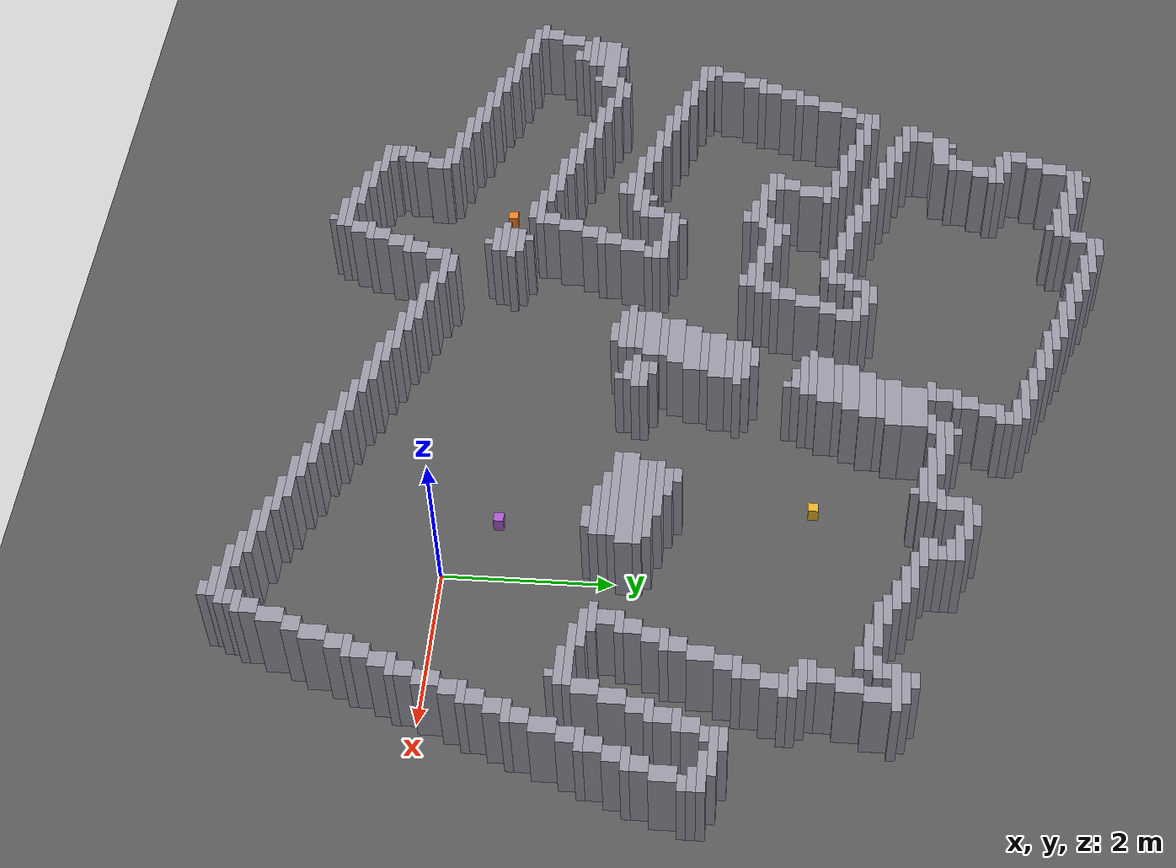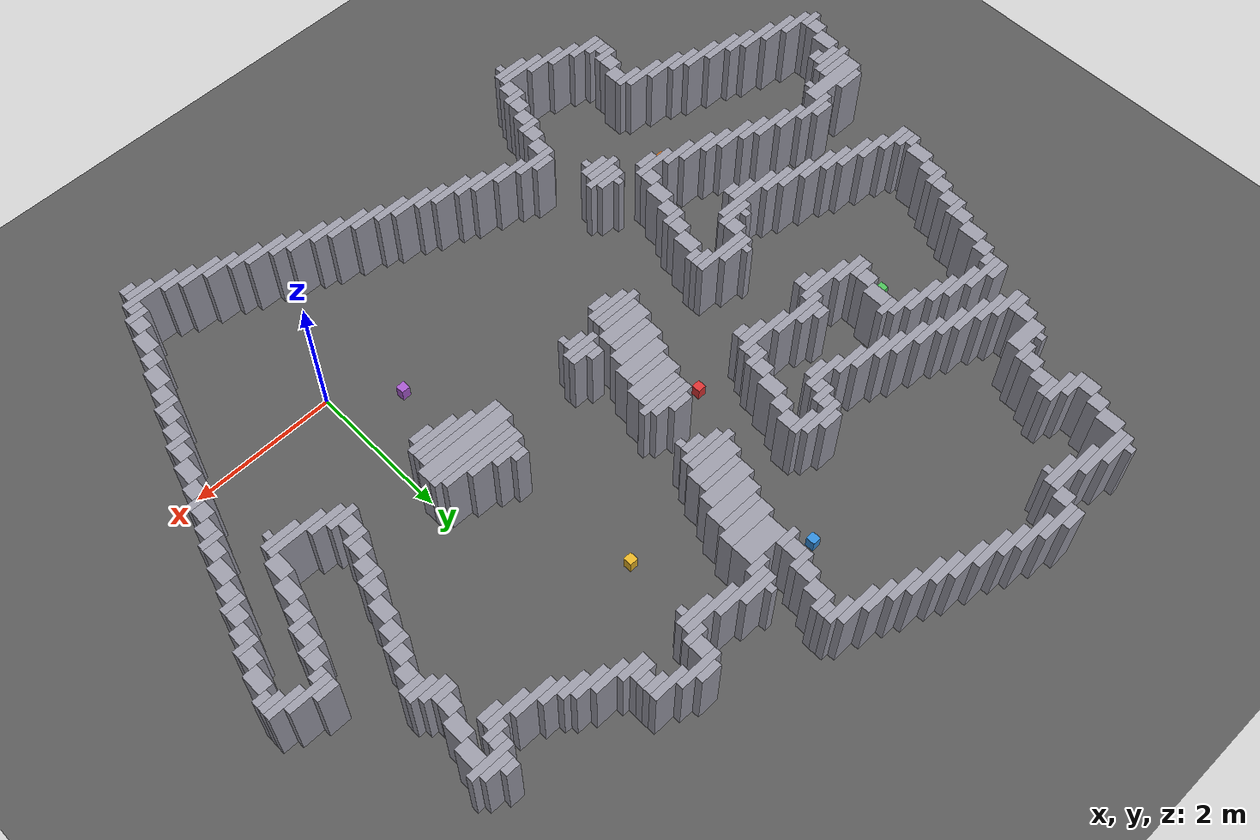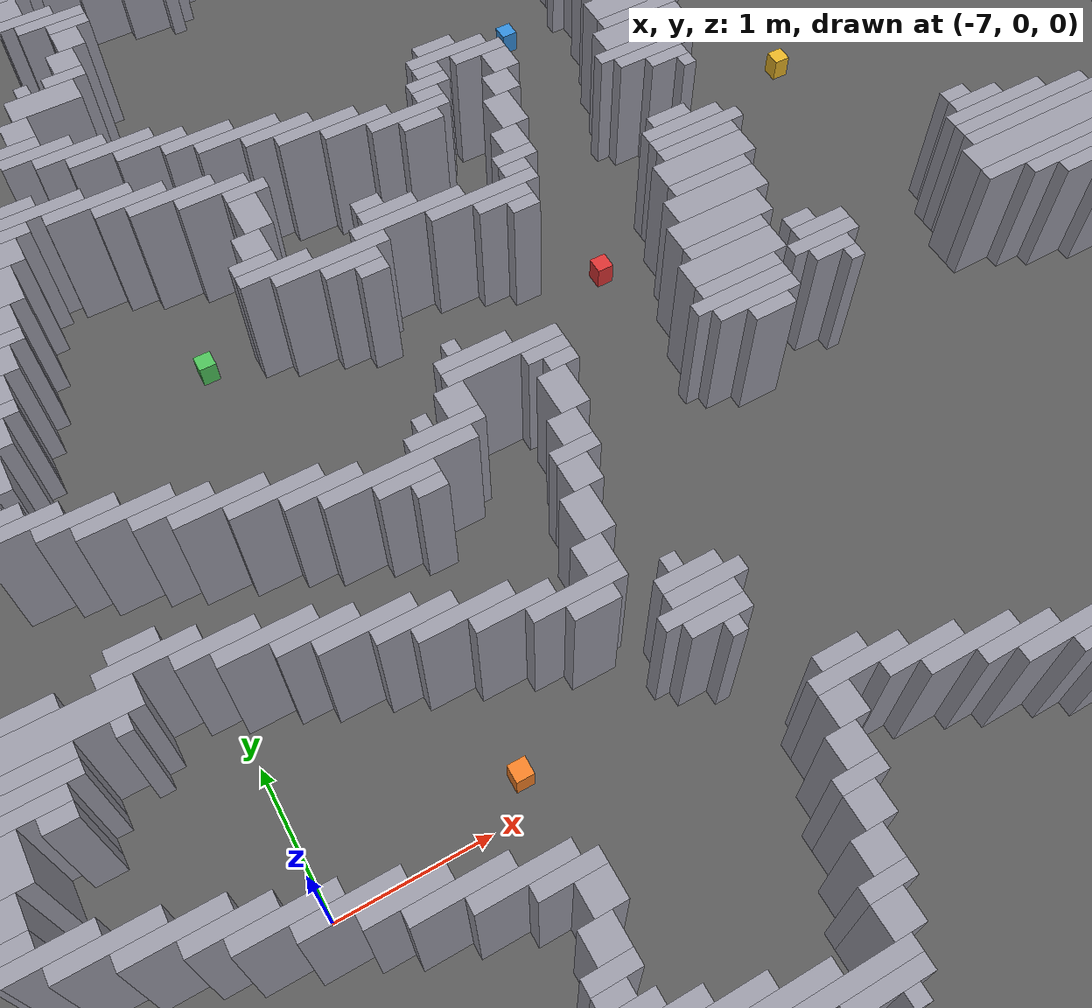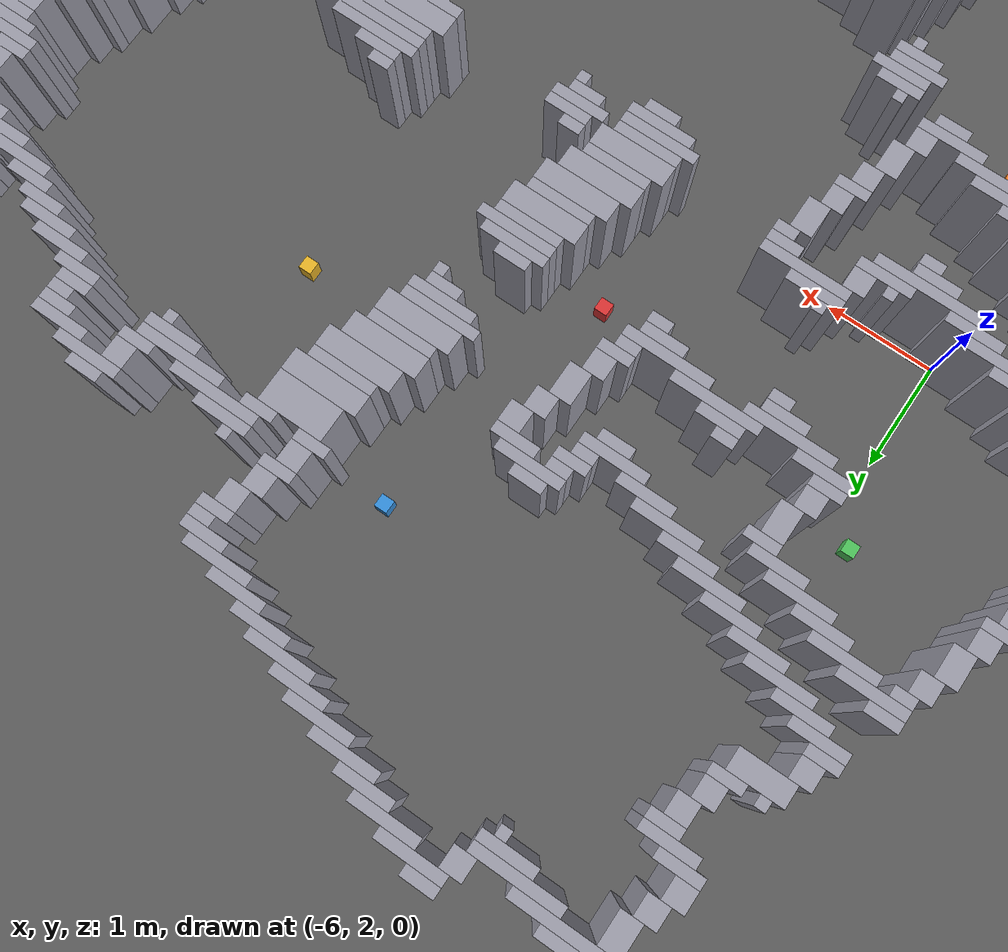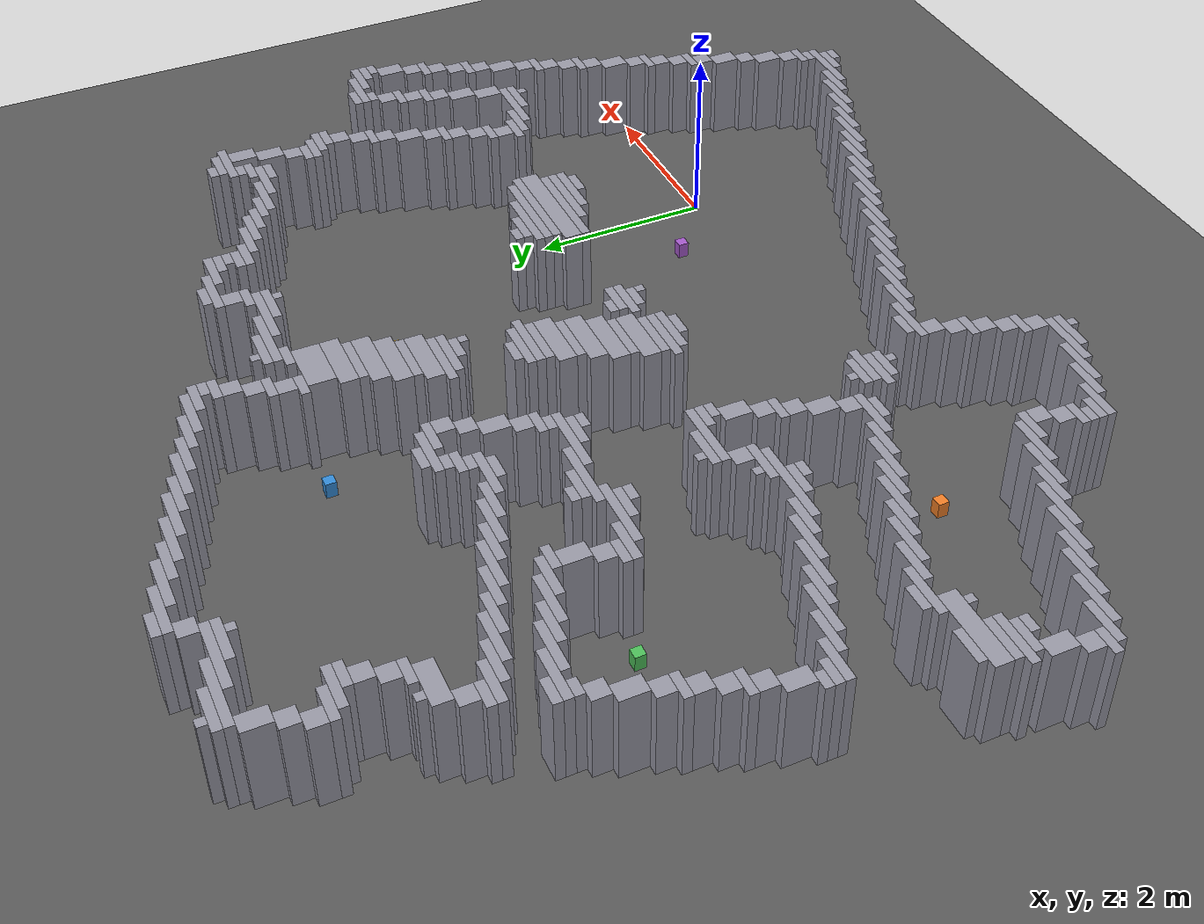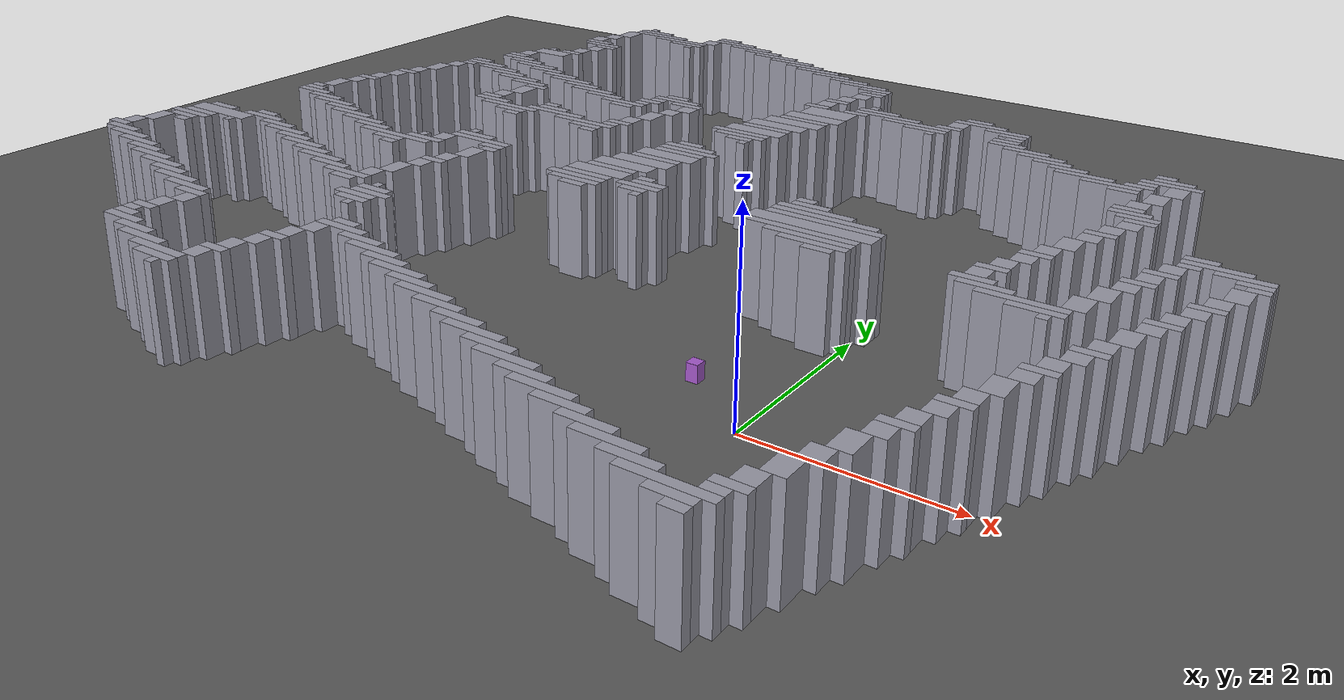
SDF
<?xml version="1.0"?>
<sdf version="1.8">
  <world name="dimi">
    <physics name="1ms" type="ignored">
      <max_step_size>0.004</max_step_size>
      <real_time_factor>1.0</real_time_factor>
    </physics>
    <plugin filename="gz-sim-physics-system" name="gz::sim::systems::Physics"/>
    <plugin filename="gz-sim-user-commands-system" name="gz::sim::systems::UserCommands"/>
    <plugin filename="gz-sim-scene-broadcaster-system" name="gz::sim::systems::SceneBroadcaster"/>
    <plugin filename="gz-sim-sensors-system" name="gz::sim::systems::Sensors">
      <render_engine>ogre2</render_engine>
    </plugin>

    <light type="directional" name="sun">
      <cast_shadows>false</cast_shadows>
      <pose>0 0 10 0 0 0</pose>
      <diffuse>0.9 0.9 0.9 1</diffuse>
      <direction>-0.3 0.2 -1</direction>
    </light>

    <model name="ground">
      <static>true</static>
      <link name="ground_link">
        <collision name="c"><geometry><plane><normal>0 0 1</normal><size>60 60</size></plane></geometry></collision>
        <visual name="v"><geometry><plane><normal>0 0 1</normal><size>60 60</size></plane></geometry>
          <material><ambient>0.3 0.3 0.3 1</ambient><diffuse>0.35 0.35 0.35 1</diffuse></material>
        </visual>
      </link>
    </model>

    <model name="walls">
      <static>true</static>
      <link name="wall_0">
        <pose>-4.8230 7.6800 0.5000 0 0 0</pose>
        <collision name="c">
          <geometry><box><size>0.3000 0.1000 1.0000</size></box></geometry>
        </collision>
        <visual name="v">
          <geometry><box><size>0.3000 0.1000 1.0000</size></box></geometry>
          <material><ambient>0.5 0.5 0.55 1</ambient><diffuse>0.6 0.6 0.65 1</diffuse></material>
        </visual>
      </link>
      <link name="wall_1">
        <pose>-6.0230 7.5800 0.5000 0 0 0</pose>
        <collision name="c">
          <geometry><box><size>0.1000 0.1000 1.0000</size></box></geometry>
        </collision>
        <visual name="v">
          <geometry><box><size>0.1000 0.1000 1.0000</size></box></geometry>
          <material><ambient>0.5 0.5 0.55 1</ambient><diffuse>0.6 0.6 0.65 1</diffuse></material>
        </visual>
      </link>
      <link name="wall_2">
        <pose>-4.6730 7.5800 0.5000 0 0 0</pose>
        <collision name="c">
          <geometry><box><size>0.6000 0.1000 1.0000</size></box></geometry>
        </collision>
        <visual name="v">
          <geometry><box><size>0.6000 0.1000 1.0000</size></box></geometry>
          <material><ambient>0.5 0.5 0.55 1</ambient><diffuse>0.6 0.6 0.65 1</diffuse></material>
        </visual>
      </link>
      <link name="wall_3">
        <pose>-5.9230 7.4800 0.5000 0 0 0</pose>
        <collision name="c">
          <geometry><box><size>0.5000 0.1000 1.0000</size></box></geometry>
        </collision>
        <visual name="v">
          <geometry><box><size>0.5000 0.1000 1.0000</size></box></geometry>
          <material><ambient>0.5 0.5 0.55 1</ambient><diffuse>0.6 0.6 0.65 1</diffuse></material>
        </visual>
      </link>
      <link name="wall_4">
        <pose>-4.9730 7.4300 0.5000 0 0 0</pose>
        <collision name="c">
          <geometry><box><size>0.2000 0.2000 1.0000</size></box></geometry>
        </collision>
        <visual name="v">
          <geometry><box><size>0.2000 0.2000 1.0000</size></box></geometry>
          <material><ambient>0.5 0.5 0.55 1</ambient><diffuse>0.6 0.6 0.65 1</diffuse></material>
        </visual>
      </link>
      <link name="wall_5">
        <pose>-4.3730 7.4800 0.5000 0 0 0</pose>
        <collision name="c">
          <geometry><box><size>0.6000 0.1000 1.0000</size></box></geometry>
        </collision>
        <visual name="v">
          <geometry><box><size>0.6000 0.1000 1.0000</size></box></geometry>
          <material><ambient>0.5 0.5 0.55 1</ambient><diffuse>0.6 0.6 0.65 1</diffuse></material>
        </visual>
      </link>
      <link name="wall_6">
        <pose>-5.7730 7.3800 0.5000 0 0 0</pose>
        <collision name="c">
          <geometry><box><size>0.8000 0.1000 1.0000</size></box></geometry>
        </collision>
        <visual name="v">
          <geometry><box><size>0.8000 0.1000 1.0000</size></box></geometry>
          <material><ambient>0.5 0.5 0.55 1</ambient><diffuse>0.6 0.6 0.65 1</diffuse></material>
        </visual>
      </link>
      <link name="wall_7">
        <pose>-4.1230 7.3800 0.5000 0 0 0</pose>
        <collision name="c">
          <geometry><box><size>0.5000 0.1000 1.0000</size></box></geometry>
        </collision>
        <visual name="v">
          <geometry><box><size>0.5000 0.1000 1.0000</size></box></geometry>
          <material><ambient>0.5 0.5 0.55 1</ambient><diffuse>0.6 0.6 0.65 1</diffuse></material>
        </visual>
      </link>
      <link name="wall_8">
        <pose>-6.1730 7.1800 0.5000 0 0 0</pose>
        <collision name="c">
          <geometry><box><size>0.2000 0.3000 1.0000</size></box></geometry>
        </collision>
        <visual name="v">
          <geometry><box><size>0.2000 0.3000 1.0000</size></box></geometry>
          <material><ambient>0.5 0.5 0.55 1</ambient><diffuse>0.6 0.6 0.65 1</diffuse></material>
        </visual>
      </link>
      <link name="wall_9">
        <pose>-5.3730 7.2800 0.5000 0 0 0</pose>
        <collision name="c">
          <geometry><box><size>0.8000 0.1000 1.0000</size></box></geometry>
        </collision>
        <visual name="v">
          <geometry><box><size>0.8000 0.1000 1.0000</size></box></geometry>
          <material><ambient>0.5 0.5 0.55 1</ambient><diffuse>0.6 0.6 0.65 1</diffuse></material>
        </visual>
      </link>
      <link name="wall_10">
        <pose>-3.8730 7.2800 0.5000 0 0 0</pose>
        <collision name="c">
          <geometry><box><size>0.6000 0.1000 1.0000</size></box></geometry>
        </collision>
        <visual name="v">
          <geometry><box><size>0.6000 0.1000 1.0000</size></box></geometry>
          <material><ambient>0.5 0.5 0.55 1</ambient><diffuse>0.6 0.6 0.65 1</diffuse></material>
        </visual>
      </link>
      <link name="wall_11">
        <pose>-5.2230 7.1800 0.5000 0 0 0</pose>
        <collision name="c">
          <geometry><box><size>0.5000 0.1000 1.0000</size></box></geometry>
        </collision>
        <visual name="v">
          <geometry><box><size>0.5000 0.1000 1.0000</size></box></geometry>
          <material><ambient>0.5 0.5 0.55 1</ambient><diffuse>0.6 0.6 0.65 1</diffuse></material>
        </visual>
      </link>
      <link name="wall_12">
        <pose>-3.5730 7.1800 0.5000 0 0 0</pose>
        <collision name="c">
          <geometry><box><size>0.6000 0.1000 1.0000</size></box></geometry>
        </collision>
        <visual name="v">
          <geometry><box><size>0.6000 0.1000 1.0000</size></box></geometry>
          <material><ambient>0.5 0.5 0.55 1</ambient><diffuse>0.6 0.6 0.65 1</diffuse></material>
        </visual>
      </link>
      <link name="wall_13">
        <pose>-5.1230 7.0800 0.5000 0 0 0</pose>
        <collision name="c">
          <geometry><box><size>0.1000 0.1000 1.0000</size></box></geometry>
        </collision>
        <visual name="v">
          <geometry><box><size>0.1000 0.1000 1.0000</size></box></geometry>
          <material><ambient>0.5 0.5 0.55 1</ambient><diffuse>0.6 0.6 0.65 1</diffuse></material>
        </visual>
      </link>
      <link name="wall_14">
        <pose>-3.3230 7.0800 0.5000 0 0 0</pose>
        <collision name="c">
          <geometry><box><size>0.5000 0.1000 1.0000</size></box></geometry>
        </collision>
        <visual name="v">
          <geometry><box><size>0.5000 0.1000 1.0000</size></box></geometry>
          <material><ambient>0.5 0.5 0.55 1</ambient><diffuse>0.6 0.6 0.65 1</diffuse></material>
        </visual>
      </link>
      <link name="wall_15">
        <pose>-6.2730 6.9300 0.5000 0 0 0</pose>
        <collision name="c">
          <geometry><box><size>0.2000 0.2000 1.0000</size></box></geometry>
        </collision>
        <visual name="v">
          <geometry><box><size>0.2000 0.2000 1.0000</size></box></geometry>
          <material><ambient>0.5 0.5 0.55 1</ambient><diffuse>0.6 0.6 0.65 1</diffuse></material>
        </visual>
      </link>
      <link name="wall_16">
        <pose>-3.0730 6.9800 0.5000 0 0 0</pose>
        <collision name="c">
          <geometry><box><size>0.6000 0.1000 1.0000</size></box></geometry>
        </collision>
        <visual name="v">
          <geometry><box><size>0.6000 0.1000 1.0000</size></box></geometry>
          <material><ambient>0.5 0.5 0.55 1</ambient><diffuse>0.6 0.6 0.65 1</diffuse></material>
        </visual>
      </link>
      <link name="wall_17">
        <pose>-2.8230 6.8800 0.5000 0 0 0</pose>
        <collision name="c">
          <geometry><box><size>0.5000 0.1000 1.0000</size></box></geometry>
        </collision>
        <visual name="v">
          <geometry><box><size>0.5000 0.1000 1.0000</size></box></geometry>
          <material><ambient>0.5 0.5 0.55 1</ambient><diffuse>0.6 0.6 0.65 1</diffuse></material>
        </visual>
      </link>
      <link name="wall_18">
        <pose>-6.3730 6.7300 0.5000 0 0 0</pose>
        <collision name="c">
          <geometry><box><size>0.2000 0.2000 1.0000</size></box></geometry>
        </collision>
        <visual name="v">
          <geometry><box><size>0.2000 0.2000 1.0000</size></box></geometry>
          <material><ambient>0.5 0.5 0.55 1</ambient><diffuse>0.6 0.6 0.65 1</diffuse></material>
        </visual>
      </link>
      <link name="wall_19">
        <pose>-2.5230 6.7800 0.5000 0 0 0</pose>
        <collision name="c">
          <geometry><box><size>0.5000 0.1000 1.0000</size></box></geometry>
        </collision>
        <visual name="v">
          <geometry><box><size>0.5000 0.1000 1.0000</size></box></geometry>
          <material><ambient>0.5 0.5 0.55 1</ambient><diffuse>0.6 0.6 0.65 1</diffuse></material>
        </visual>
      </link>
      <link name="wall_20">
        <pose>-2.2730 6.6800 0.5000 0 0 0</pose>
        <collision name="c">
          <geometry><box><size>0.6000 0.1000 1.0000</size></box></geometry>
        </collision>
        <visual name="v">
          <geometry><box><size>0.6000 0.1000 1.0000</size></box></geometry>
          <material><ambient>0.5 0.5 0.55 1</ambient><diffuse>0.6 0.6 0.65 1</diffuse></material>
        </visual>
      </link>
      <link name="wall_21">
        <pose>-6.2730 6.5800 0.5000 0 0 0</pose>
        <collision name="c">
          <geometry><box><size>0.4000 0.1000 1.0000</size></box></geometry>
        </collision>
        <visual name="v">
          <geometry><box><size>0.4000 0.1000 1.0000</size></box></geometry>
          <material><ambient>0.5 0.5 0.55 1</ambient><diffuse>0.6 0.6 0.65 1</diffuse></material>
        </visual>
      </link>
      <link name="wall_22">
        <pose>-2.0730 6.5800 0.5000 0 0 0</pose>
        <collision name="c">
          <geometry><box><size>0.4000 0.1000 1.0000</size></box></geometry>
        </collision>
        <visual name="v">
          <geometry><box><size>0.4000 0.1000 1.0000</size></box></geometry>
          <material><ambient>0.5 0.5 0.55 1</ambient><diffuse>0.6 0.6 0.65 1</diffuse></material>
        </visual>
      </link>
      <link name="wall_23">
        <pose>-6.1230 6.4800 0.5000 0 0 0</pose>
        <collision name="c">
          <geometry><box><size>0.5000 0.1000 1.0000</size></box></geometry>
        </collision>
        <visual name="v">
          <geometry><box><size>0.5000 0.1000 1.0000</size></box></geometry>
          <material><ambient>0.5 0.5 0.55 1</ambient><diffuse>0.6 0.6 0.65 1</diffuse></material>
        </visual>
      </link>
      <link name="wall_24">
        <pose>-1.9730 6.4800 0.5000 0 0 0</pose>
        <collision name="c">
          <geometry><box><size>0.2000 0.1000 1.0000</size></box></geometry>
        </collision>
        <visual name="v">
          <geometry><box><size>0.2000 0.1000 1.0000</size></box></geometry>
          <material><ambient>0.5 0.5 0.55 1</ambient><diffuse>0.6 0.6 0.65 1</diffuse></material>
        </visual>
      </link>
      <link name="wall_25">
        <pose>-6.0230 6.3800 0.5000 0 0 0</pose>
        <collision name="c">
          <geometry><box><size>0.3000 0.1000 1.0000</size></box></geometry>
        </collision>
        <visual name="v">
          <geometry><box><size>0.3000 0.1000 1.0000</size></box></geometry>
          <material><ambient>0.5 0.5 0.55 1</ambient><diffuse>0.6 0.6 0.65 1</diffuse></material>
        </visual>
      </link>
      <link name="wall_26">
        <pose>-2.0230 6.3800 0.5000 0 0 0</pose>
        <collision name="c">
          <geometry><box><size>0.3000 0.1000 1.0000</size></box></geometry>
        </collision>
        <visual name="v">
          <geometry><box><size>0.3000 0.1000 1.0000</size></box></geometry>
          <material><ambient>0.5 0.5 0.55 1</ambient><diffuse>0.6 0.6 0.65 1</diffuse></material>
        </visual>
      </link>
      <link name="wall_27">
        <pose>-6.0730 6.2300 0.5000 0 0 0</pose>
        <collision name="c">
          <geometry><box><size>0.2000 0.2000 1.0000</size></box></geometry>
        </collision>
        <visual name="v">
          <geometry><box><size>0.2000 0.2000 1.0000</size></box></geometry>
          <material><ambient>0.5 0.5 0.55 1</ambient><diffuse>0.6 0.6 0.65 1</diffuse></material>
        </visual>
      </link>
      <link name="wall_28">
        <pose>-2.0730 6.2300 0.5000 0 0 0</pose>
        <collision name="c">
          <geometry><box><size>0.2000 0.2000 1.0000</size></box></geometry>
        </collision>
        <visual name="v">
          <geometry><box><size>0.2000 0.2000 1.0000</size></box></geometry>
          <material><ambient>0.5 0.5 0.55 1</ambient><diffuse>0.6 0.6 0.65 1</diffuse></material>
        </visual>
      </link>
      <link name="wall_29">
        <pose>-6.1730 6.0300 0.5000 0 0 0</pose>
        <collision name="c">
          <geometry><box><size>0.2000 0.2000 1.0000</size></box></geometry>
        </collision>
        <visual name="v">
          <geometry><box><size>0.2000 0.2000 1.0000</size></box></geometry>
          <material><ambient>0.5 0.5 0.55 1</ambient><diffuse>0.6 0.6 0.65 1</diffuse></material>
        </visual>
      </link>
      <link name="wall_30">
        <pose>-2.1730 6.0300 0.5000 0 0 0</pose>
        <collision name="c">
          <geometry><box><size>0.2000 0.2000 1.0000</size></box></geometry>
        </collision>
        <visual name="v">
          <geometry><box><size>0.2000 0.2000 1.0000</size></box></geometry>
          <material><ambient>0.5 0.5 0.55 1</ambient><diffuse>0.6 0.6 0.65 1</diffuse></material>
        </visual>
      </link>
      <link name="wall_31">
        <pose>-0.5230 6.0800 0.5000 0 0 0</pose>
        <collision name="c">
          <geometry><box><size>0.3000 0.1000 1.0000</size></box></geometry>
        </collision>
        <visual name="v">
          <geometry><box><size>0.3000 0.1000 1.0000</size></box></geometry>
          <material><ambient>0.5 0.5 0.55 1</ambient><diffuse>0.6 0.6 0.65 1</diffuse></material>
        </visual>
      </link>
      <link name="wall_32">
        <pose>-0.4730 5.9800 0.5000 0 0 0</pose>
        <collision name="c">
          <geometry><box><size>0.6000 0.1000 1.0000</size></box></geometry>
        </collision>
        <visual name="v">
          <geometry><box><size>0.6000 0.1000 1.0000</size></box></geometry>
          <material><ambient>0.5 0.5 0.55 1</ambient><diffuse>0.6 0.6 0.65 1</diffuse></material>
        </visual>
      </link>
      <link name="wall_33">
        <pose>-6.5230 5.8800 0.5000 0 0 0</pose>
        <collision name="c">
          <geometry><box><size>0.1000 0.1000 1.0000</size></box></geometry>
        </collision>
        <visual name="v">
          <geometry><box><size>0.1000 0.1000 1.0000</size></box></geometry>
          <material><ambient>0.5 0.5 0.55 1</ambient><diffuse>0.6 0.6 0.65 1</diffuse></material>
        </visual>
      </link>
      <link name="wall_34">
        <pose>-6.2230 5.8800 0.5000 0 0 0</pose>
        <collision name="c">
          <geometry><box><size>0.3000 0.1000 1.0000</size></box></geometry>
        </collision>
        <visual name="v">
          <geometry><box><size>0.3000 0.1000 1.0000</size></box></geometry>
          <material><ambient>0.5 0.5 0.55 1</ambient><diffuse>0.6 0.6 0.65 1</diffuse></material>
        </visual>
      </link>
      <link name="wall_35">
        <pose>-2.2230 5.8800 0.5000 0 0 0</pose>
        <collision name="c">
          <geometry><box><size>0.3000 0.1000 1.0000</size></box></geometry>
        </collision>
        <visual name="v">
          <geometry><box><size>0.3000 0.1000 1.0000</size></box></geometry>
          <material><ambient>0.5 0.5 0.55 1</ambient><diffuse>0.6 0.6 0.65 1</diffuse></material>
        </visual>
      </link>
      <link name="wall_36">
        <pose>-1.7230 5.8800 0.5000 0 0 0</pose>
        <collision name="c">
          <geometry><box><size>0.1000 0.1000 1.0000</size></box></geometry>
        </collision>
        <visual name="v">
          <geometry><box><size>0.1000 0.1000 1.0000</size></box></geometry>
          <material><ambient>0.5 0.5 0.55 1</ambient><diffuse>0.6 0.6 0.65 1</diffuse></material>
        </visual>
      </link>
      <link name="wall_37">
        <pose>-0.6730 5.8300 0.5000 0 0 0</pose>
        <collision name="c">
          <geometry><box><size>0.2000 0.2000 1.0000</size></box></geometry>
        </collision>
        <visual name="v">
          <geometry><box><size>0.2000 0.2000 1.0000</size></box></geometry>
          <material><ambient>0.5 0.5 0.55 1</ambient><diffuse>0.6 0.6 0.65 1</diffuse></material>
        </visual>
      </link>
      <link name="wall_38">
        <pose>-0.1230 5.8800 0.5000 0 0 0</pose>
        <collision name="c">
          <geometry><box><size>0.5000 0.1000 1.0000</size></box></geometry>
        </collision>
        <visual name="v">
          <geometry><box><size>0.5000 0.1000 1.0000</size></box></geometry>
          <material><ambient>0.5 0.5 0.55 1</ambient><diffuse>0.6 0.6 0.65 1</diffuse></material>
        </visual>
      </link>
      <link name="wall_39">
        <pose>-6.4230 5.7300 0.5000 0 0 0</pose>
        <collision name="c">
          <geometry><box><size>0.5000 0.2000 1.0000</size></box></geometry>
        </collision>
        <visual name="v">
          <geometry><box><size>0.5000 0.2000 1.0000</size></box></geometry>
          <material><ambient>0.5 0.5 0.55 1</ambient><diffuse>0.6 0.6 0.65 1</diffuse></material>
        </visual>
      </link>
      <link name="wall_40">
        <pose>-2.2730 5.7300 0.5000 0 0 0</pose>
        <collision name="c">
          <geometry><box><size>0.2000 0.2000 1.0000</size></box></geometry>
        </collision>
        <visual name="v">
          <geometry><box><size>0.2000 0.2000 1.0000</size></box></geometry>
          <material><ambient>0.5 0.5 0.55 1</ambient><diffuse>0.6 0.6 0.65 1</diffuse></material>
        </visual>
      </link>
      <link name="wall_41">
        <pose>-1.6230 5.7800 0.5000 0 0 0</pose>
        <collision name="c">
          <geometry><box><size>0.5000 0.1000 1.0000</size></box></geometry>
        </collision>
        <visual name="v">
          <geometry><box><size>0.5000 0.1000 1.0000</size></box></geometry>
          <material><ambient>0.5 0.5 0.55 1</ambient><diffuse>0.6 0.6 0.65 1</diffuse></material>
        </visual>
      </link>
      <link name="wall_42">
        <pose>-0.0230 5.7800 0.5000 0 0 0</pose>
        <collision name="c">
          <geometry><box><size>0.3000 0.1000 1.0000</size></box></geometry>
        </collision>
        <visual name="v">
          <geometry><box><size>0.3000 0.1000 1.0000</size></box></geometry>
          <material><ambient>0.5 0.5 0.55 1</ambient><diffuse>0.6 0.6 0.65 1</diffuse></material>
        </visual>
      </link>
      <link name="wall_43">
        <pose>-1.4730 5.6800 0.5000 0 0 0</pose>
        <collision name="c">
          <geometry><box><size>0.8000 0.1000 1.0000</size></box></geometry>
        </collision>
        <visual name="v">
          <geometry><box><size>0.8000 0.1000 1.0000</size></box></geometry>
          <material><ambient>0.5 0.5 0.55 1</ambient><diffuse>0.6 0.6 0.65 1</diffuse></material>
        </visual>
      </link>
      <link name="wall_44">
        <pose>-0.7230 5.6800 0.5000 0 0 0</pose>
        <collision name="c">
          <geometry><box><size>0.3000 0.1000 1.0000</size></box></geometry>
        </collision>
        <visual name="v">
          <geometry><box><size>0.3000 0.1000 1.0000</size></box></geometry>
          <material><ambient>0.5 0.5 0.55 1</ambient><diffuse>0.6 0.6 0.65 1</diffuse></material>
        </visual>
      </link>
      <link name="wall_45">
        <pose>0.0270 5.6800 0.5000 0 0 0</pose>
        <collision name="c">
          <geometry><box><size>0.2000 0.1000 1.0000</size></box></geometry>
        </collision>
        <visual name="v">
          <geometry><box><size>0.2000 0.1000 1.0000</size></box></geometry>
          <material><ambient>0.5 0.5 0.55 1</ambient><diffuse>0.6 0.6 0.65 1</diffuse></material>
        </visual>
      </link>
      <link name="wall_46">
        <pose>-6.6730 5.5300 0.5000 0 0 0</pose>
        <collision name="c">
          <geometry><box><size>0.2000 0.2000 1.0000</size></box></geometry>
        </collision>
        <visual name="v">
          <geometry><box><size>0.2000 0.2000 1.0000</size></box></geometry>
          <material><ambient>0.5 0.5 0.55 1</ambient><diffuse>0.6 0.6 0.65 1</diffuse></material>
        </visual>
      </link>
      <link name="wall_47">
        <pose>-2.3230 5.5800 0.5000 0 0 0</pose>
        <collision name="c">
          <geometry><box><size>0.3000 0.1000 1.0000</size></box></geometry>
        </collision>
        <visual name="v">
          <geometry><box><size>0.3000 0.1000 1.0000</size></box></geometry>
          <material><ambient>0.5 0.5 0.55 1</ambient><diffuse>0.6 0.6 0.65 1</diffuse></material>
        </visual>
      </link>
      <link name="wall_48">
        <pose>-1.8230 5.5800 0.5000 0 0 0</pose>
        <collision name="c">
          <geometry><box><size>0.3000 0.1000 1.0000</size></box></geometry>
        </collision>
        <visual name="v">
          <geometry><box><size>0.3000 0.1000 1.0000</size></box></geometry>
          <material><ambient>0.5 0.5 0.55 1</ambient><diffuse>0.6 0.6 0.65 1</diffuse></material>
        </visual>
      </link>
      <link name="wall_49">
        <pose>-1.0730 5.5800 0.5000 0 0 0</pose>
        <collision name="c">
          <geometry><box><size>0.8000 0.1000 1.0000</size></box></geometry>
        </collision>
        <visual name="v">
          <geometry><box><size>0.8000 0.1000 1.0000</size></box></geometry>
          <material><ambient>0.5 0.5 0.55 1</ambient><diffuse>0.6 0.6 0.65 1</diffuse></material>
        </visual>
      </link>
      <link name="wall_50">
        <pose>-0.0230 5.5800 0.5000 0 0 0</pose>
        <collision name="c">
          <geometry><box><size>0.3000 0.1000 1.0000</size></box></geometry>
        </collision>
        <visual name="v">
          <geometry><box><size>0.3000 0.1000 1.0000</size></box></geometry>
          <material><ambient>0.5 0.5 0.55 1</ambient><diffuse>0.6 0.6 0.65 1</diffuse></material>
        </visual>
      </link>
      <link name="wall_51">
        <pose>-2.0730 5.3800 0.5000 0 0 0</pose>
        <collision name="c">
          <geometry><box><size>0.6000 0.3000 1.0000</size></box></geometry>
        </collision>
        <visual name="v">
          <geometry><box><size>0.6000 0.3000 1.0000</size></box></geometry>
          <material><ambient>0.5 0.5 0.55 1</ambient><diffuse>0.6 0.6 0.65 1</diffuse></material>
        </visual>
      </link>
      <link name="wall_52">
        <pose>-0.9230 5.4800 0.5000 0 0 0</pose>
        <collision name="c">
          <geometry><box><size>0.5000 0.1000 1.0000</size></box></geometry>
        </collision>
        <visual name="v">
          <geometry><box><size>0.5000 0.1000 1.0000</size></box></geometry>
          <material><ambient>0.5 0.5 0.55 1</ambient><diffuse>0.6 0.6 0.65 1</diffuse></material>
        </visual>
      </link>
      <link name="wall_53">
        <pose>0.0270 5.4800 0.5000 0 0 0</pose>
        <collision name="c">
          <geometry><box><size>0.4000 0.1000 1.0000</size></box></geometry>
        </collision>
        <visual name="v">
          <geometry><box><size>0.4000 0.1000 1.0000</size></box></geometry>
          <material><ambient>0.5 0.5 0.55 1</ambient><diffuse>0.6 0.6 0.65 1</diffuse></material>
        </visual>
      </link>
      <link name="wall_54">
        <pose>-6.7230 5.3800 0.5000 0 0 0</pose>
        <collision name="c">
          <geometry><box><size>0.3000 0.1000 1.0000</size></box></geometry>
        </collision>
        <visual name="v">
          <geometry><box><size>0.3000 0.1000 1.0000</size></box></geometry>
          <material><ambient>0.5 0.5 0.55 1</ambient><diffuse>0.6 0.6 0.65 1</diffuse></material>
        </visual>
      </link>
      <link name="wall_55">
        <pose>-0.8230 5.3800 0.5000 0 0 0</pose>
        <collision name="c">
          <geometry><box><size>0.1000 0.1000 1.0000</size></box></geometry>
        </collision>
        <visual name="v">
          <geometry><box><size>0.1000 0.1000 1.0000</size></box></geometry>
          <material><ambient>0.5 0.5 0.55 1</ambient><diffuse>0.6 0.6 0.65 1</diffuse></material>
        </visual>
      </link>
      <link name="wall_56">
        <pose>0.2770 5.3800 0.5000 0 0 0</pose>
        <collision name="c">
          <geometry><box><size>0.5000 0.1000 1.0000</size></box></geometry>
        </collision>
        <visual name="v">
          <geometry><box><size>0.5000 0.1000 1.0000</size></box></geometry>
          <material><ambient>0.5 0.5 0.55 1</ambient><diffuse>0.6 0.6 0.65 1</diffuse></material>
        </visual>
      </link>
      <link name="wall_57">
        <pose>1.7270 5.3800 0.5000 0 0 0</pose>
        <collision name="c">
          <geometry><box><size>0.2000 0.1000 1.0000</size></box></geometry>
        </collision>
        <visual name="v">
          <geometry><box><size>0.2000 0.1000 1.0000</size></box></geometry>
          <material><ambient>0.5 0.5 0.55 1</ambient><diffuse>0.6 0.6 0.65 1</diffuse></material>
        </visual>
      </link>
      <link name="wall_58">
        <pose>-6.6230 5.2800 0.5000 0 0 0</pose>
        <collision name="c">
          <geometry><box><size>0.5000 0.1000 1.0000</size></box></geometry>
        </collision>
        <visual name="v">
          <geometry><box><size>0.5000 0.1000 1.0000</size></box></geometry>
          <material><ambient>0.5 0.5 0.55 1</ambient><diffuse>0.6 0.6 0.65 1</diffuse></material>
        </visual>
      </link>
      <link name="wall_59">
        <pose>0.4770 5.2800 0.5000 0 0 0</pose>
        <collision name="c">
          <geometry><box><size>0.5000 0.1000 1.0000</size></box></geometry>
        </collision>
        <visual name="v">
          <geometry><box><size>0.5000 0.1000 1.0000</size></box></geometry>
          <material><ambient>0.5 0.5 0.55 1</ambient><diffuse>0.6 0.6 0.65 1</diffuse></material>
        </visual>
      </link>
      <link name="wall_60">
        <pose>1.8270 5.2800 0.5000 0 0 0</pose>
        <collision name="c">
          <geometry><box><size>0.4000 0.1000 1.0000</size></box></geometry>
        </collision>
        <visual name="v">
          <geometry><box><size>0.4000 0.1000 1.0000</size></box></geometry>
          <material><ambient>0.5 0.5 0.55 1</ambient><diffuse>0.6 0.6 0.65 1</diffuse></material>
        </visual>
      </link>
      <link name="wall_61">
        <pose>-6.4230 5.1800 0.5000 0 0 0</pose>
        <collision name="c">
          <geometry><box><size>0.5000 0.1000 1.0000</size></box></geometry>
        </collision>
        <visual name="v">
          <geometry><box><size>0.5000 0.1000 1.0000</size></box></geometry>
          <material><ambient>0.5 0.5 0.55 1</ambient><diffuse>0.6 0.6 0.65 1</diffuse></material>
        </visual>
      </link>
      <link name="wall_62">
        <pose>-2.1230 5.1300 0.5000 0 0 0</pose>
        <collision name="c">
          <geometry><box><size>0.7000 0.2000 1.0000</size></box></geometry>
        </collision>
        <visual name="v">
          <geometry><box><size>0.7000 0.2000 1.0000</size></box></geometry>
          <material><ambient>0.5 0.5 0.55 1</ambient><diffuse>0.6 0.6 0.65 1</diffuse></material>
        </visual>
      </link>
      <link name="wall_63">
        <pose>0.6270 5.1800 0.5000 0 0 0</pose>
        <collision name="c">
          <geometry><box><size>0.4000 0.1000 1.0000</size></box></geometry>
        </collision>
        <visual name="v">
          <geometry><box><size>0.4000 0.1000 1.0000</size></box></geometry>
          <material><ambient>0.5 0.5 0.55 1</ambient><diffuse>0.6 0.6 0.65 1</diffuse></material>
        </visual>
      </link>
      <link name="wall_64">
        <pose>1.8270 5.1800 0.5000 0 0 0</pose>
        <collision name="c">
          <geometry><box><size>0.6000 0.1000 1.0000</size></box></geometry>
        </collision>
        <visual name="v">
          <geometry><box><size>0.6000 0.1000 1.0000</size></box></geometry>
          <material><ambient>0.5 0.5 0.55 1</ambient><diffuse>0.6 0.6 0.65 1</diffuse></material>
        </visual>
      </link>
      <link name="wall_65">
        <pose>-6.1730 5.0800 0.5000 0 0 0</pose>
        <collision name="c">
          <geometry><box><size>0.6000 0.1000 1.0000</size></box></geometry>
        </collision>
        <visual name="v">
          <geometry><box><size>0.6000 0.1000 1.0000</size></box></geometry>
          <material><ambient>0.5 0.5 0.55 1</ambient><diffuse>0.6 0.6 0.65 1</diffuse></material>
        </visual>
      </link>
      <link name="wall_66">
        <pose>0.8270 5.0800 0.5000 0 0 0</pose>
        <collision name="c">
          <geometry><box><size>0.4000 0.1000 1.0000</size></box></geometry>
        </collision>
        <visual name="v">
          <geometry><box><size>0.4000 0.1000 1.0000</size></box></geometry>
          <material><ambient>0.5 0.5 0.55 1</ambient><diffuse>0.6 0.6 0.65 1</diffuse></material>
        </visual>
      </link>
      <link name="wall_67">
        <pose>1.6270 5.0800 0.5000 0 0 0</pose>
        <collision name="c">
          <geometry><box><size>0.2000 0.1000 1.0000</size></box></geometry>
        </collision>
        <visual name="v">
          <geometry><box><size>0.2000 0.1000 1.0000</size></box></geometry>
          <material><ambient>0.5 0.5 0.55 1</ambient><diffuse>0.6 0.6 0.65 1</diffuse></material>
        </visual>
      </link>
      <link name="wall_68">
        <pose>1.9270 4.9800 0.5000 0 0 0</pose>
        <collision name="c">
          <geometry><box><size>0.2000 0.3000 1.0000</size></box></geometry>
        </collision>
        <visual name="v">
          <geometry><box><size>0.2000 0.3000 1.0000</size></box></geometry>
          <material><ambient>0.5 0.5 0.55 1</ambient><diffuse>0.6 0.6 0.65 1</diffuse></material>
        </visual>
      </link>
      <link name="wall_69">
        <pose>-5.9230 4.9800 0.5000 0 0 0</pose>
        <collision name="c">
          <geometry><box><size>0.5000 0.1000 1.0000</size></box></geometry>
        </collision>
        <visual name="v">
          <geometry><box><size>0.5000 0.1000 1.0000</size></box></geometry>
          <material><ambient>0.5 0.5 0.55 1</ambient><diffuse>0.6 0.6 0.65 1</diffuse></material>
        </visual>
      </link>
      <link name="wall_70">
        <pose>-2.1730 4.9800 0.5000 0 0 0</pose>
        <collision name="c">
          <geometry><box><size>0.6000 0.1000 1.0000</size></box></geometry>
        </collision>
        <visual name="v">
          <geometry><box><size>0.6000 0.1000 1.0000</size></box></geometry>
          <material><ambient>0.5 0.5 0.55 1</ambient><diffuse>0.6 0.6 0.65 1</diffuse></material>
        </visual>
      </link>
      <link name="wall_71">
        <pose>1.0270 4.9800 0.5000 0 0 0</pose>
        <collision name="c">
          <geometry><box><size>0.6000 0.1000 1.0000</size></box></geometry>
        </collision>
        <visual name="v">
          <geometry><box><size>0.6000 0.1000 1.0000</size></box></geometry>
          <material><ambient>0.5 0.5 0.55 1</ambient><diffuse>0.6 0.6 0.65 1</diffuse></material>
        </visual>
      </link>
      <link name="wall_72">
        <pose>1.5770 4.9800 0.5000 0 0 0</pose>
        <collision name="c">
          <geometry><box><size>0.3000 0.1000 1.0000</size></box></geometry>
        </collision>
        <visual name="v">
          <geometry><box><size>0.3000 0.1000 1.0000</size></box></geometry>
          <material><ambient>0.5 0.5 0.55 1</ambient><diffuse>0.6 0.6 0.65 1</diffuse></material>
        </visual>
      </link>
      <link name="wall_73">
        <pose>-6.9230 4.8800 0.5000 0 0 0</pose>
        <collision name="c">
          <geometry><box><size>0.3000 0.1000 1.0000</size></box></geometry>
        </collision>
        <visual name="v">
          <geometry><box><size>0.3000 0.1000 1.0000</size></box></geometry>
          <material><ambient>0.5 0.5 0.55 1</ambient><diffuse>0.6 0.6 0.65 1</diffuse></material>
        </visual>
      </link>
      <link name="wall_74">
        <pose>-5.6230 4.8800 0.5000 0 0 0</pose>
        <collision name="c">
          <geometry><box><size>0.5000 0.1000 1.0000</size></box></geometry>
        </collision>
        <visual name="v">
          <geometry><box><size>0.5000 0.1000 1.0000</size></box></geometry>
          <material><ambient>0.5 0.5 0.55 1</ambient><diffuse>0.6 0.6 0.65 1</diffuse></material>
        </visual>
      </link>
      <link name="wall_75">
        <pose>-3.8230 4.8800 0.5000 0 0 0</pose>
        <collision name="c">
          <geometry><box><size>0.3000 0.1000 1.0000</size></box></geometry>
        </collision>
        <visual name="v">
          <geometry><box><size>0.3000 0.1000 1.0000</size></box></geometry>
          <material><ambient>0.5 0.5 0.55 1</ambient><diffuse>0.6 0.6 0.65 1</diffuse></material>
        </visual>
      </link>
      <link name="wall_76">
        <pose>-2.2230 4.8300 0.5000 0 0 0</pose>
        <collision name="c">
          <geometry><box><size>0.7000 0.2000 1.0000</size></box></geometry>
        </collision>
        <visual name="v">
          <geometry><box><size>0.7000 0.2000 1.0000</size></box></geometry>
          <material><ambient>0.5 0.5 0.55 1</ambient><diffuse>0.6 0.6 0.65 1</diffuse></material>
        </visual>
      </link>
      <link name="wall_77">
        <pose>1.3270 4.8800 0.5000 0 0 0</pose>
        <collision name="c">
          <geometry><box><size>0.6000 0.1000 1.0000</size></box></geometry>
        </collision>
        <visual name="v">
          <geometry><box><size>0.6000 0.1000 1.0000</size></box></geometry>
          <material><ambient>0.5 0.5 0.55 1</ambient><diffuse>0.6 0.6 0.65 1</diffuse></material>
        </visual>
      </link>
      <link name="wall_78">
        <pose>-6.7730 4.7800 0.5000 0 0 0</pose>
        <collision name="c">
          <geometry><box><size>0.6000 0.1000 1.0000</size></box></geometry>
        </collision>
        <visual name="v">
          <geometry><box><size>0.6000 0.1000 1.0000</size></box></geometry>
          <material><ambient>0.5 0.5 0.55 1</ambient><diffuse>0.6 0.6 0.65 1</diffuse></material>
        </visual>
      </link>
      <link name="wall_79">
        <pose>-5.3730 4.7800 0.5000 0 0 0</pose>
        <collision name="c">
          <geometry><box><size>0.6000 0.1000 1.0000</size></box></geometry>
        </collision>
        <visual name="v">
          <geometry><box><size>0.6000 0.1000 1.0000</size></box></geometry>
          <material><ambient>0.5 0.5 0.55 1</ambient><diffuse>0.6 0.6 0.65 1</diffuse></material>
        </visual>
      </link>
      <link name="wall_80">
        <pose>-3.7730 4.7800 0.5000 0 0 0</pose>
        <collision name="c">
          <geometry><box><size>0.6000 0.1000 1.0000</size></box></geometry>
        </collision>
        <visual name="v">
          <geometry><box><size>0.6000 0.1000 1.0000</size></box></geometry>
          <material><ambient>0.5 0.5 0.55 1</ambient><diffuse>0.6 0.6 0.65 1</diffuse></material>
        </visual>
      </link>
      <link name="wall_81">
        <pose>1.4770 4.7800 0.5000 0 0 0</pose>
        <collision name="c">
          <geometry><box><size>0.3000 0.1000 1.0000</size></box></geometry>
        </collision>
        <visual name="v">
          <geometry><box><size>0.3000 0.1000 1.0000</size></box></geometry>
          <material><ambient>0.5 0.5 0.55 1</ambient><diffuse>0.6 0.6 0.65 1</diffuse></material>
        </visual>
      </link>
      <link name="wall_82">
        <pose>1.8270 4.6800 0.5000 0 0 0</pose>
        <collision name="c">
          <geometry><box><size>0.2000 0.3000 1.0000</size></box></geometry>
        </collision>
        <visual name="v">
          <geometry><box><size>0.2000 0.3000 1.0000</size></box></geometry>
          <material><ambient>0.5 0.5 0.55 1</ambient><diffuse>0.6 0.6 0.65 1</diffuse></material>
        </visual>
      </link>
      <link name="wall_83">
        <pose>-6.9730 4.6800 0.5000 0 0 0</pose>
        <collision name="c">
          <geometry><box><size>0.2000 0.1000 1.0000</size></box></geometry>
        </collision>
        <visual name="v">
          <geometry><box><size>0.2000 0.1000 1.0000</size></box></geometry>
          <material><ambient>0.5 0.5 0.55 1</ambient><diffuse>0.6 0.6 0.65 1</diffuse></material>
        </visual>
      </link>
      <link name="wall_84">
        <pose>-6.4730 4.6800 0.5000 0 0 0</pose>
        <collision name="c">
          <geometry><box><size>0.6000 0.1000 1.0000</size></box></geometry>
        </collision>
        <visual name="v">
          <geometry><box><size>0.6000 0.1000 1.0000</size></box></geometry>
          <material><ambient>0.5 0.5 0.55 1</ambient><diffuse>0.6 0.6 0.65 1</diffuse></material>
        </visual>
      </link>
      <link name="wall_85">
        <pose>-5.1230 4.6800 0.5000 0 0 0</pose>
        <collision name="c">
          <geometry><box><size>0.5000 0.1000 1.0000</size></box></geometry>
        </collision>
        <visual name="v">
          <geometry><box><size>0.5000 0.1000 1.0000</size></box></geometry>
          <material><ambient>0.5 0.5 0.55 1</ambient><diffuse>0.6 0.6 0.65 1</diffuse></material>
        </visual>
      </link>
      <link name="wall_86">
        <pose>-3.9730 4.6800 0.5000 0 0 0</pose>
        <collision name="c">
          <geometry><box><size>0.2000 0.1000 1.0000</size></box></geometry>
        </collision>
        <visual name="v">
          <geometry><box><size>0.2000 0.1000 1.0000</size></box></geometry>
          <material><ambient>0.5 0.5 0.55 1</ambient><diffuse>0.6 0.6 0.65 1</diffuse></material>
        </visual>
      </link>
      <link name="wall_87">
        <pose>-3.5730 4.6800 0.5000 0 0 0</pose>
        <collision name="c">
          <geometry><box><size>0.4000 0.1000 1.0000</size></box></geometry>
        </collision>
        <visual name="v">
          <geometry><box><size>0.4000 0.1000 1.0000</size></box></geometry>
          <material><ambient>0.5 0.5 0.55 1</ambient><diffuse>0.6 0.6 0.65 1</diffuse></material>
        </visual>
      </link>
      <link name="wall_88">
        <pose>-2.3230 4.6300 0.5000 0 0 0</pose>
        <collision name="c">
          <geometry><box><size>0.7000 0.2000 1.0000</size></box></geometry>
        </collision>
        <visual name="v">
          <geometry><box><size>0.7000 0.2000 1.0000</size></box></geometry>
          <material><ambient>0.5 0.5 0.55 1</ambient><diffuse>0.6 0.6 0.65 1</diffuse></material>
        </visual>
      </link>
      <link name="wall_89">
        <pose>-7.0730 4.5300 0.5000 0 0 0</pose>
        <collision name="c">
          <geometry><box><size>0.2000 0.2000 1.0000</size></box></geometry>
        </collision>
        <visual name="v">
          <geometry><box><size>0.2000 0.2000 1.0000</size></box></geometry>
          <material><ambient>0.5 0.5 0.55 1</ambient><diffuse>0.6 0.6 0.65 1</diffuse></material>
        </visual>
      </link>
      <link name="wall_90">
        <pose>-6.2230 4.5800 0.5000 0 0 0</pose>
        <collision name="c">
          <geometry><box><size>0.5000 0.1000 1.0000</size></box></geometry>
        </collision>
        <visual name="v">
          <geometry><box><size>0.5000 0.1000 1.0000</size></box></geometry>
          <material><ambient>0.5 0.5 0.55 1</ambient><diffuse>0.6 0.6 0.65 1</diffuse></material>
        </visual>
      </link>
      <link name="wall_91">
        <pose>-4.8730 4.5800 0.5000 0 0 0</pose>
        <collision name="c">
          <geometry><box><size>0.6000 0.1000 1.0000</size></box></geometry>
        </collision>
        <visual name="v">
          <geometry><box><size>0.6000 0.1000 1.0000</size></box></geometry>
          <material><ambient>0.5 0.5 0.55 1</ambient><diffuse>0.6 0.6 0.65 1</diffuse></material>
        </visual>
      </link>
      <link name="wall_92">
        <pose>-4.0230 4.5800 0.5000 0 0 0</pose>
        <collision name="c">
          <geometry><box><size>0.3000 0.1000 1.0000</size></box></geometry>
        </collision>
        <visual name="v">
          <geometry><box><size>0.3000 0.1000 1.0000</size></box></geometry>
          <material><ambient>0.5 0.5 0.55 1</ambient><diffuse>0.6 0.6 0.65 1</diffuse></material>
        </visual>
      </link>
      <link name="wall_93">
        <pose>-3.4730 4.5300 0.5000 0 0 0</pose>
        <collision name="c">
          <geometry><box><size>0.2000 0.2000 1.0000</size></box></geometry>
        </collision>
        <visual name="v">
          <geometry><box><size>0.2000 0.2000 1.0000</size></box></geometry>
          <material><ambient>0.5 0.5 0.55 1</ambient><diffuse>0.6 0.6 0.65 1</diffuse></material>
        </visual>
      </link>
      <link name="wall_94">
        <pose>-5.9730 4.4800 0.5000 0 0 0</pose>
        <collision name="c">
          <geometry><box><size>0.6000 0.1000 1.0000</size></box></geometry>
        </collision>
        <visual name="v">
          <geometry><box><size>0.6000 0.1000 1.0000</size></box></geometry>
          <material><ambient>0.5 0.5 0.55 1</ambient><diffuse>0.6 0.6 0.65 1</diffuse></material>
        </visual>
      </link>
      <link name="wall_95">
        <pose>-4.6230 4.4800 0.5000 0 0 0</pose>
        <collision name="c">
          <geometry><box><size>0.5000 0.1000 1.0000</size></box></geometry>
        </collision>
        <visual name="v">
          <geometry><box><size>0.5000 0.1000 1.0000</size></box></geometry>
          <material><ambient>0.5 0.5 0.55 1</ambient><diffuse>0.6 0.6 0.65 1</diffuse></material>
        </visual>
      </link>
      <link name="wall_96">
        <pose>-4.0730 4.4800 0.5000 0 0 0</pose>
        <collision name="c">
          <geometry><box><size>0.2000 0.1000 1.0000</size></box></geometry>
        </collision>
        <visual name="v">
          <geometry><box><size>0.2000 0.1000 1.0000</size></box></geometry>
          <material><ambient>0.5 0.5 0.55 1</ambient><diffuse>0.6 0.6 0.65 1</diffuse></material>
        </visual>
      </link>
      <link name="wall_97">
        <pose>-2.3730 4.4800 0.5000 0 0 0</pose>
        <collision name="c">
          <geometry><box><size>0.6000 0.1000 1.0000</size></box></geometry>
        </collision>
        <visual name="v">
          <geometry><box><size>0.6000 0.1000 1.0000</size></box></geometry>
          <material><ambient>0.5 0.5 0.55 1</ambient><diffuse>0.6 0.6 0.65 1</diffuse></material>
        </visual>
      </link>
      <link name="wall_98">
        <pose>1.7270 4.4300 0.5000 0 0 0</pose>
        <collision name="c">
          <geometry><box><size>0.2000 0.2000 1.0000</size></box></geometry>
        </collision>
        <visual name="v">
          <geometry><box><size>0.2000 0.2000 1.0000</size></box></geometry>
          <material><ambient>0.5 0.5 0.55 1</ambient><diffuse>0.6 0.6 0.65 1</diffuse></material>
        </visual>
      </link>
      <link name="wall_99">
        <pose>-7.1730 4.2800 0.5000 0 0 0</pose>
        <collision name="c">
          <geometry><box><size>0.2000 0.3000 1.0000</size></box></geometry>
        </collision>
        <visual name="v">
          <geometry><box><size>0.2000 0.3000 1.0000</size></box></geometry>
          <material><ambient>0.5 0.5 0.55 1</ambient><diffuse>0.6 0.6 0.65 1</diffuse></material>
        </visual>
      </link>
      <link name="wall_100">
        <pose>-5.7230 4.3800 0.5000 0 0 0</pose>
        <collision name="c">
          <geometry><box><size>0.5000 0.1000 1.0000</size></box></geometry>
        </collision>
        <visual name="v">
          <geometry><box><size>0.5000 0.1000 1.0000</size></box></geometry>
          <material><ambient>0.5 0.5 0.55 1</ambient><diffuse>0.6 0.6 0.65 1</diffuse></material>
        </visual>
      </link>
      <link name="wall_101">
        <pose>-4.2730 4.3800 0.5000 0 0 0</pose>
        <collision name="c">
          <geometry><box><size>0.6000 0.1000 1.0000</size></box></geometry>
        </collision>
        <visual name="v">
          <geometry><box><size>0.6000 0.1000 1.0000</size></box></geometry>
          <material><ambient>0.5 0.5 0.55 1</ambient><diffuse>0.6 0.6 0.65 1</diffuse></material>
        </visual>
      </link>
      <link name="wall_102">
        <pose>-3.5730 4.3300 0.5000 0 0 0</pose>
        <collision name="c">
          <geometry><box><size>0.2000 0.2000 1.0000</size></box></geometry>
        </collision>
        <visual name="v">
          <geometry><box><size>0.2000 0.2000 1.0000</size></box></geometry>
          <material><ambient>0.5 0.5 0.55 1</ambient><diffuse>0.6 0.6 0.65 1</diffuse></material>
        </visual>
      </link>
      <link name="wall_103">
        <pose>-2.4230 4.3300 0.5000 0 0 0</pose>
        <collision name="c">
          <geometry><box><size>0.7000 0.2000 1.0000</size></box></geometry>
        </collision>
        <visual name="v">
          <geometry><box><size>0.7000 0.2000 1.0000</size></box></geometry>
          <material><ambient>0.5 0.5 0.55 1</ambient><diffuse>0.6 0.6 0.65 1</diffuse></material>
        </visual>
      </link>
      <link name="wall_104">
        <pose>-5.5230 4.2800 0.5000 0 0 0</pose>
        <collision name="c">
          <geometry><box><size>0.3000 0.1000 1.0000</size></box></geometry>
        </collision>
        <visual name="v">
          <geometry><box><size>0.3000 0.1000 1.0000</size></box></geometry>
          <material><ambient>0.5 0.5 0.55 1</ambient><diffuse>0.6 0.6 0.65 1</diffuse></material>
        </visual>
      </link>
      <link name="wall_105">
        <pose>-4.2230 4.2800 0.5000 0 0 0</pose>
        <collision name="c">
          <geometry><box><size>0.3000 0.1000 1.0000</size></box></geometry>
        </collision>
        <visual name="v">
          <geometry><box><size>0.3000 0.1000 1.0000</size></box></geometry>
          <material><ambient>0.5 0.5 0.55 1</ambient><diffuse>0.6 0.6 0.65 1</diffuse></material>
        </visual>
      </link>
      <link name="wall_106">
        <pose>1.6770 4.2800 0.5000 0 0 0</pose>
        <collision name="c">
          <geometry><box><size>0.3000 0.1000 1.0000</size></box></geometry>
        </collision>
        <visual name="v">
          <geometry><box><size>0.3000 0.1000 1.0000</size></box></geometry>
          <material><ambient>0.5 0.5 0.55 1</ambient><diffuse>0.6 0.6 0.65 1</diffuse></material>
        </visual>
      </link>
      <link name="wall_107">
        <pose>-5.5730 4.0800 0.5000 0 0 0</pose>
        <collision name="c">
          <geometry><box><size>0.2000 0.3000 1.0000</size></box></geometry>
        </collision>
        <visual name="v">
          <geometry><box><size>0.2000 0.3000 1.0000</size></box></geometry>
          <material><ambient>0.5 0.5 0.55 1</ambient><diffuse>0.6 0.6 0.65 1</diffuse></material>
        </visual>
      </link>
      <link name="wall_108">
        <pose>-3.6730 4.0800 0.5000 0 0 0</pose>
        <collision name="c">
          <geometry><box><size>0.2000 0.3000 1.0000</size></box></geometry>
        </collision>
        <visual name="v">
          <geometry><box><size>0.2000 0.3000 1.0000</size></box></geometry>
          <material><ambient>0.5 0.5 0.55 1</ambient><diffuse>0.6 0.6 0.65 1</diffuse></material>
        </visual>
      </link>
      <link name="wall_109">
        <pose>-2.5230 4.1800 0.5000 0 0 0</pose>
        <collision name="c">
          <geometry><box><size>0.7000 0.1000 1.0000</size></box></geometry>
        </collision>
        <visual name="v">
          <geometry><box><size>0.7000 0.1000 1.0000</size></box></geometry>
          <material><ambient>0.5 0.5 0.55 1</ambient><diffuse>0.6 0.6 0.65 1</diffuse></material>
        </visual>
      </link>
      <link name="wall_110">
        <pose>1.7270 4.1800 0.5000 0 0 0</pose>
        <collision name="c">
          <geometry><box><size>0.4000 0.1000 1.0000</size></box></geometry>
        </collision>
        <visual name="v">
          <geometry><box><size>0.4000 0.1000 1.0000</size></box></geometry>
          <material><ambient>0.5 0.5 0.55 1</ambient><diffuse>0.6 0.6 0.65 1</diffuse></material>
        </visual>
      </link>
      <link name="wall_111">
        <pose>-7.2730 4.0300 0.5000 0 0 0</pose>
        <collision name="c">
          <geometry><box><size>0.2000 0.2000 1.0000</size></box></geometry>
        </collision>
        <visual name="v">
          <geometry><box><size>0.2000 0.2000 1.0000</size></box></geometry>
          <material><ambient>0.5 0.5 0.55 1</ambient><diffuse>0.6 0.6 0.65 1</diffuse></material>
        </visual>
      </link>
      <link name="wall_112">
        <pose>-2.4730 4.0800 0.5000 0 0 0</pose>
        <collision name="c">
          <geometry><box><size>0.6000 0.1000 1.0000</size></box></geometry>
        </collision>
        <visual name="v">
          <geometry><box><size>0.6000 0.1000 1.0000</size></box></geometry>
          <material><ambient>0.5 0.5 0.55 1</ambient><diffuse>0.6 0.6 0.65 1</diffuse></material>
        </visual>
      </link>
      <link name="wall_113">
        <pose>1.8270 4.0800 0.5000 0 0 0</pose>
        <collision name="c">
          <geometry><box><size>0.4000 0.1000 1.0000</size></box></geometry>
        </collision>
        <visual name="v">
          <geometry><box><size>0.4000 0.1000 1.0000</size></box></geometry>
          <material><ambient>0.5 0.5 0.55 1</ambient><diffuse>0.6 0.6 0.65 1</diffuse></material>
        </visual>
      </link>
      <link name="wall_114">
        <pose>-2.4230 3.9800 0.5000 0 0 0</pose>
        <collision name="c">
          <geometry><box><size>0.3000 0.1000 1.0000</size></box></geometry>
        </collision>
        <visual name="v">
          <geometry><box><size>0.3000 0.1000 1.0000</size></box></geometry>
          <material><ambient>0.5 0.5 0.55 1</ambient><diffuse>0.6 0.6 0.65 1</diffuse></material>
        </visual>
      </link>
      <link name="wall_115">
        <pose>1.8770 3.9800 0.5000 0 0 0</pose>
        <collision name="c">
          <geometry><box><size>0.3000 0.1000 1.0000</size></box></geometry>
        </collision>
        <visual name="v">
          <geometry><box><size>0.3000 0.1000 1.0000</size></box></geometry>
          <material><ambient>0.5 0.5 0.55 1</ambient><diffuse>0.6 0.6 0.65 1</diffuse></material>
        </visual>
      </link>
      <link name="wall_116">
        <pose>-7.3230 3.8800 0.5000 0 0 0</pose>
        <collision name="c">
          <geometry><box><size>0.3000 0.1000 1.0000</size></box></geometry>
        </collision>
        <visual name="v">
          <geometry><box><size>0.3000 0.1000 1.0000</size></box></geometry>
          <material><ambient>0.5 0.5 0.55 1</ambient><diffuse>0.6 0.6 0.65 1</diffuse></material>
        </visual>
      </link>
      <link name="wall_117">
        <pose>-5.6730 3.8300 0.5000 0 0 0</pose>
        <collision name="c">
          <geometry><box><size>0.2000 0.2000 1.0000</size></box></geometry>
        </collision>
        <visual name="v">
          <geometry><box><size>0.2000 0.2000 1.0000</size></box></geometry>
          <material><ambient>0.5 0.5 0.55 1</ambient><diffuse>0.6 0.6 0.65 1</diffuse></material>
        </visual>
      </link>
      <link name="wall_118">
        <pose>-3.7730 3.8300 0.5000 0 0 0</pose>
        <collision name="c">
          <geometry><box><size>0.2000 0.2000 1.0000</size></box></geometry>
        </collision>
        <visual name="v">
          <geometry><box><size>0.2000 0.2000 1.0000</size></box></geometry>
          <material><ambient>0.5 0.5 0.55 1</ambient><diffuse>0.6 0.6 0.65 1</diffuse></material>
        </visual>
      </link>
      <link name="wall_119">
        <pose>-2.3230 3.8800 0.5000 0 0 0</pose>
        <collision name="c">
          <geometry><box><size>0.1000 0.1000 1.0000</size></box></geometry>
        </collision>
        <visual name="v">
          <geometry><box><size>0.1000 0.1000 1.0000</size></box></geometry>
          <material><ambient>0.5 0.5 0.55 1</ambient><diffuse>0.6 0.6 0.65 1</diffuse></material>
        </visual>
      </link>
      <link name="wall_120">
        <pose>1.8270 3.8300 0.5000 0 0 0</pose>
        <collision name="c">
          <geometry><box><size>0.2000 0.2000 1.0000</size></box></geometry>
        </collision>
        <visual name="v">
          <geometry><box><size>0.2000 0.2000 1.0000</size></box></geometry>
          <material><ambient>0.5 0.5 0.55 1</ambient><diffuse>0.6 0.6 0.65 1</diffuse></material>
        </visual>
      </link>
      <link name="wall_121">
        <pose>-7.3730 3.7300 0.5000 0 0 0</pose>
        <collision name="c">
          <geometry><box><size>0.2000 0.2000 1.0000</size></box></geometry>
        </collision>
        <visual name="v">
          <geometry><box><size>0.2000 0.2000 1.0000</size></box></geometry>
          <material><ambient>0.5 0.5 0.55 1</ambient><diffuse>0.6 0.6 0.65 1</diffuse></material>
        </visual>
      </link>
      <link name="wall_122">
        <pose>-4.8730 3.7800 0.5000 0 0 0</pose>
        <collision name="c">
          <geometry><box><size>0.2000 0.1000 1.0000</size></box></geometry>
        </collision>
        <visual name="v">
          <geometry><box><size>0.2000 0.1000 1.0000</size></box></geometry>
          <material><ambient>0.5 0.5 0.55 1</ambient><diffuse>0.6 0.6 0.65 1</diffuse></material>
        </visual>
      </link>
      <link name="wall_123">
        <pose>-5.7230 3.6800 0.5000 0 0 0</pose>
        <collision name="c">
          <geometry><box><size>0.3000 0.1000 1.0000</size></box></geometry>
        </collision>
        <visual name="v">
          <geometry><box><size>0.3000 0.1000 1.0000</size></box></geometry>
          <material><ambient>0.5 0.5 0.55 1</ambient><diffuse>0.6 0.6 0.65 1</diffuse></material>
        </visual>
      </link>
      <link name="wall_124">
        <pose>-4.7730 3.6800 0.5000 0 0 0</pose>
        <collision name="c">
          <geometry><box><size>0.4000 0.1000 1.0000</size></box></geometry>
        </collision>
        <visual name="v">
          <geometry><box><size>0.4000 0.1000 1.0000</size></box></geometry>
          <material><ambient>0.5 0.5 0.55 1</ambient><diffuse>0.6 0.6 0.65 1</diffuse></material>
        </visual>
      </link>
      <link name="wall_125">
        <pose>-3.8230 3.6800 0.5000 0 0 0</pose>
        <collision name="c">
          <geometry><box><size>0.3000 0.1000 1.0000</size></box></geometry>
        </collision>
        <visual name="v">
          <geometry><box><size>0.3000 0.1000 1.0000</size></box></geometry>
          <material><ambient>0.5 0.5 0.55 1</ambient><diffuse>0.6 0.6 0.65 1</diffuse></material>
        </visual>
      </link>
      <link name="wall_126">
        <pose>1.7270 3.6300 0.5000 0 0 0</pose>
        <collision name="c">
          <geometry><box><size>0.2000 0.2000 1.0000</size></box></geometry>
        </collision>
        <visual name="v">
          <geometry><box><size>0.2000 0.2000 1.0000</size></box></geometry>
          <material><ambient>0.5 0.5 0.55 1</ambient><diffuse>0.6 0.6 0.65 1</diffuse></material>
        </visual>
      </link>
      <link name="wall_127">
        <pose>-7.4730 3.5300 0.5000 0 0 0</pose>
        <collision name="c">
          <geometry><box><size>0.2000 0.2000 1.0000</size></box></geometry>
        </collision>
        <visual name="v">
          <geometry><box><size>0.2000 0.2000 1.0000</size></box></geometry>
          <material><ambient>0.5 0.5 0.55 1</ambient><diffuse>0.6 0.6 0.65 1</diffuse></material>
        </visual>
      </link>
      <link name="wall_128">
        <pose>-5.6230 3.5800 0.5000 0 0 0</pose>
        <collision name="c">
          <geometry><box><size>0.5000 0.1000 1.0000</size></box></geometry>
        </collision>
        <visual name="v">
          <geometry><box><size>0.5000 0.1000 1.0000</size></box></geometry>
          <material><ambient>0.5 0.5 0.55 1</ambient><diffuse>0.6 0.6 0.65 1</diffuse></material>
        </visual>
      </link>
      <link name="wall_129">
        <pose>-4.6730 3.5800 0.5000 0 0 0</pose>
        <collision name="c">
          <geometry><box><size>0.8000 0.1000 1.0000</size></box></geometry>
        </collision>
        <visual name="v">
          <geometry><box><size>0.8000 0.1000 1.0000</size></box></geometry>
          <material><ambient>0.5 0.5 0.55 1</ambient><diffuse>0.6 0.6 0.65 1</diffuse></material>
        </visual>
      </link>
      <link name="wall_130">
        <pose>-3.8730 3.5800 0.5000 0 0 0</pose>
        <collision name="c">
          <geometry><box><size>0.2000 0.1000 1.0000</size></box></geometry>
        </collision>
        <visual name="v">
          <geometry><box><size>0.2000 0.1000 1.0000</size></box></geometry>
          <material><ambient>0.5 0.5 0.55 1</ambient><diffuse>0.6 0.6 0.65 1</diffuse></material>
        </visual>
      </link>
      <link name="wall_131">
        <pose>-5.2730 3.4800 0.5000 0 0 0</pose>
        <collision name="c">
          <geometry><box><size>0.8000 0.1000 1.0000</size></box></geometry>
        </collision>
        <visual name="v">
          <geometry><box><size>0.8000 0.1000 1.0000</size></box></geometry>
          <material><ambient>0.5 0.5 0.55 1</ambient><diffuse>0.6 0.6 0.65 1</diffuse></material>
        </visual>
      </link>
      <link name="wall_132">
        <pose>-4.1730 3.4800 0.5000 0 0 0</pose>
        <collision name="c">
          <geometry><box><size>0.8000 0.1000 1.0000</size></box></geometry>
        </collision>
        <visual name="v">
          <geometry><box><size>0.8000 0.1000 1.0000</size></box></geometry>
          <material><ambient>0.5 0.5 0.55 1</ambient><diffuse>0.6 0.6 0.65 1</diffuse></material>
        </visual>
      </link>
      <link name="wall_133">
        <pose>-2.7230 3.4800 0.5000 0 0 0</pose>
        <collision name="c">
          <geometry><box><size>0.3000 0.1000 1.0000</size></box></geometry>
        </collision>
        <visual name="v">
          <geometry><box><size>0.3000 0.1000 1.0000</size></box></geometry>
          <material><ambient>0.5 0.5 0.55 1</ambient><diffuse>0.6 0.6 0.65 1</diffuse></material>
        </visual>
      </link>
      <link name="wall_134">
        <pose>1.6770 3.4800 0.5000 0 0 0</pose>
        <collision name="c">
          <geometry><box><size>0.3000 0.1000 1.0000</size></box></geometry>
        </collision>
        <visual name="v">
          <geometry><box><size>0.3000 0.1000 1.0000</size></box></geometry>
          <material><ambient>0.5 0.5 0.55 1</ambient><diffuse>0.6 0.6 0.65 1</diffuse></material>
        </visual>
      </link>
      <link name="wall_135">
        <pose>-7.5230 3.3800 0.5000 0 0 0</pose>
        <collision name="c">
          <geometry><box><size>0.3000 0.1000 1.0000</size></box></geometry>
        </collision>
        <visual name="v">
          <geometry><box><size>0.3000 0.1000 1.0000</size></box></geometry>
          <material><ambient>0.5 0.5 0.55 1</ambient><diffuse>0.6 0.6 0.65 1</diffuse></material>
        </visual>
      </link>
      <link name="wall_136">
        <pose>-5.1730 3.3800 0.5000 0 0 0</pose>
        <collision name="c">
          <geometry><box><size>0.4000 0.1000 1.0000</size></box></geometry>
        </collision>
        <visual name="v">
          <geometry><box><size>0.4000 0.1000 1.0000</size></box></geometry>
          <material><ambient>0.5 0.5 0.55 1</ambient><diffuse>0.6 0.6 0.65 1</diffuse></material>
        </visual>
      </link>
      <link name="wall_137">
        <pose>-4.0730 3.3800 0.5000 0 0 0</pose>
        <collision name="c">
          <geometry><box><size>0.4000 0.1000 1.0000</size></box></geometry>
        </collision>
        <visual name="v">
          <geometry><box><size>0.4000 0.1000 1.0000</size></box></geometry>
          <material><ambient>0.5 0.5 0.55 1</ambient><diffuse>0.6 0.6 0.65 1</diffuse></material>
        </visual>
      </link>
      <link name="wall_138">
        <pose>-2.6730 3.3800 0.5000 0 0 0</pose>
        <collision name="c">
          <geometry><box><size>0.6000 0.1000 1.0000</size></box></geometry>
        </collision>
        <visual name="v">
          <geometry><box><size>0.6000 0.1000 1.0000</size></box></geometry>
          <material><ambient>0.5 0.5 0.55 1</ambient><diffuse>0.6 0.6 0.65 1</diffuse></material>
        </visual>
      </link>
      <link name="wall_139">
        <pose>1.6270 3.3300 0.5000 0 0 0</pose>
        <collision name="c">
          <geometry><box><size>0.2000 0.2000 1.0000</size></box></geometry>
        </collision>
        <visual name="v">
          <geometry><box><size>0.2000 0.2000 1.0000</size></box></geometry>
          <material><ambient>0.5 0.5 0.55 1</ambient><diffuse>0.6 0.6 0.65 1</diffuse></material>
        </visual>
      </link>
      <link name="wall_140">
        <pose>2.5770 3.3800 0.5000 0 0 0</pose>
        <collision name="c">
          <geometry><box><size>0.3000 0.1000 1.0000</size></box></geometry>
        </collision>
        <visual name="v">
          <geometry><box><size>0.3000 0.1000 1.0000</size></box></geometry>
          <material><ambient>0.5 0.5 0.55 1</ambient><diffuse>0.6 0.6 0.65 1</diffuse></material>
        </visual>
      </link>
      <link name="wall_141">
        <pose>-7.5730 3.2300 0.5000 0 0 0</pose>
        <collision name="c">
          <geometry><box><size>0.2000 0.2000 1.0000</size></box></geometry>
        </collision>
        <visual name="v">
          <geometry><box><size>0.2000 0.2000 1.0000</size></box></geometry>
          <material><ambient>0.5 0.5 0.55 1</ambient><diffuse>0.6 0.6 0.65 1</diffuse></material>
        </visual>
      </link>
      <link name="wall_142">
        <pose>-5.0730 3.2800 0.5000 0 0 0</pose>
        <collision name="c">
          <geometry><box><size>0.2000 0.1000 1.0000</size></box></geometry>
        </collision>
        <visual name="v">
          <geometry><box><size>0.2000 0.1000 1.0000</size></box></geometry>
          <material><ambient>0.5 0.5 0.55 1</ambient><diffuse>0.6 0.6 0.65 1</diffuse></material>
        </visual>
      </link>
      <link name="wall_143">
        <pose>-3.9730 3.2800 0.5000 0 0 0</pose>
        <collision name="c">
          <geometry><box><size>0.2000 0.1000 1.0000</size></box></geometry>
        </collision>
        <visual name="v">
          <geometry><box><size>0.2000 0.1000 1.0000</size></box></geometry>
          <material><ambient>0.5 0.5 0.55 1</ambient><diffuse>0.6 0.6 0.65 1</diffuse></material>
        </visual>
      </link>
      <link name="wall_144">
        <pose>-2.6230 3.2800 0.5000 0 0 0</pose>
        <collision name="c">
          <geometry><box><size>0.7000 0.1000 1.0000</size></box></geometry>
        </collision>
        <visual name="v">
          <geometry><box><size>0.7000 0.1000 1.0000</size></box></geometry>
          <material><ambient>0.5 0.5 0.55 1</ambient><diffuse>0.6 0.6 0.65 1</diffuse></material>
        </visual>
      </link>
      <link name="wall_145">
        <pose>2.7270 3.2800 0.5000 0 0 0</pose>
        <collision name="c">
          <geometry><box><size>0.6000 0.1000 1.0000</size></box></geometry>
        </collision>
        <visual name="v">
          <geometry><box><size>0.6000 0.1000 1.0000</size></box></geometry>
          <material><ambient>0.5 0.5 0.55 1</ambient><diffuse>0.6 0.6 0.65 1</diffuse></material>
        </visual>
      </link>
      <link name="wall_146">
        <pose>-2.6730 3.1800 0.5000 0 0 0</pose>
        <collision name="c">
          <geometry><box><size>0.6000 0.1000 1.0000</size></box></geometry>
        </collision>
        <visual name="v">
          <geometry><box><size>0.6000 0.1000 1.0000</size></box></geometry>
          <material><ambient>0.5 0.5 0.55 1</ambient><diffuse>0.6 0.6 0.65 1</diffuse></material>
        </visual>
      </link>
      <link name="wall_147">
        <pose>1.5270 3.0800 0.5000 0 0 0</pose>
        <collision name="c">
          <geometry><box><size>0.2000 0.3000 1.0000</size></box></geometry>
        </collision>
        <visual name="v">
          <geometry><box><size>0.2000 0.3000 1.0000</size></box></geometry>
          <material><ambient>0.5 0.5 0.55 1</ambient><diffuse>0.6 0.6 0.65 1</diffuse></material>
        </visual>
      </link>
      <link name="wall_148">
        <pose>2.5270 3.1800 0.5000 0 0 0</pose>
        <collision name="c">
          <geometry><box><size>0.2000 0.1000 1.0000</size></box></geometry>
        </collision>
        <visual name="v">
          <geometry><box><size>0.2000 0.1000 1.0000</size></box></geometry>
          <material><ambient>0.5 0.5 0.55 1</ambient><diffuse>0.6 0.6 0.65 1</diffuse></material>
        </visual>
      </link>
      <link name="wall_149">
        <pose>2.9770 3.1800 0.5000 0 0 0</pose>
        <collision name="c">
          <geometry><box><size>0.5000 0.1000 1.0000</size></box></geometry>
        </collision>
        <visual name="v">
          <geometry><box><size>0.5000 0.1000 1.0000</size></box></geometry>
          <material><ambient>0.5 0.5 0.55 1</ambient><diffuse>0.6 0.6 0.65 1</diffuse></material>
        </visual>
      </link>
      <link name="wall_150">
        <pose>-7.6730 2.9800 0.5000 0 0 0</pose>
        <collision name="c">
          <geometry><box><size>0.2000 0.3000 1.0000</size></box></geometry>
        </collision>
        <visual name="v">
          <geometry><box><size>0.2000 0.3000 1.0000</size></box></geometry>
          <material><ambient>0.5 0.5 0.55 1</ambient><diffuse>0.6 0.6 0.65 1</diffuse></material>
        </visual>
      </link>
      <link name="wall_151">
        <pose>-2.7230 3.0300 0.5000 0 0 0</pose>
        <collision name="c">
          <geometry><box><size>0.7000 0.2000 1.0000</size></box></geometry>
        </collision>
        <visual name="v">
          <geometry><box><size>0.7000 0.2000 1.0000</size></box></geometry>
          <material><ambient>0.5 0.5 0.55 1</ambient><diffuse>0.6 0.6 0.65 1</diffuse></material>
        </visual>
      </link>
      <link name="wall_152">
        <pose>2.4270 3.0300 0.5000 0 0 0</pose>
        <collision name="c">
          <geometry><box><size>0.2000 0.2000 1.0000</size></box></geometry>
        </collision>
        <visual name="v">
          <geometry><box><size>0.2000 0.2000 1.0000</size></box></geometry>
          <material><ambient>0.5 0.5 0.55 1</ambient><diffuse>0.6 0.6 0.65 1</diffuse></material>
        </visual>
      </link>
      <link name="wall_153">
        <pose>3.0770 3.0800 0.5000 0 0 0</pose>
        <collision name="c">
          <geometry><box><size>0.3000 0.1000 1.0000</size></box></geometry>
        </collision>
        <visual name="v">
          <geometry><box><size>0.3000 0.1000 1.0000</size></box></geometry>
          <material><ambient>0.5 0.5 0.55 1</ambient><diffuse>0.6 0.6 0.65 1</diffuse></material>
        </visual>
      </link>
      <link name="wall_154">
        <pose>3.1270 2.9800 0.5000 0 0 0</pose>
        <collision name="c">
          <geometry><box><size>0.2000 0.1000 1.0000</size></box></geometry>
        </collision>
        <visual name="v">
          <geometry><box><size>0.2000 0.1000 1.0000</size></box></geometry>
          <material><ambient>0.5 0.5 0.55 1</ambient><diffuse>0.6 0.6 0.65 1</diffuse></material>
        </visual>
      </link>
      <link name="wall_155">
        <pose>-2.7730 2.8800 0.5000 0 0 0</pose>
        <collision name="c">
          <geometry><box><size>0.6000 0.1000 1.0000</size></box></geometry>
        </collision>
        <visual name="v">
          <geometry><box><size>0.6000 0.1000 1.0000</size></box></geometry>
          <material><ambient>0.5 0.5 0.55 1</ambient><diffuse>0.6 0.6 0.65 1</diffuse></material>
        </visual>
      </link>
      <link name="wall_156">
        <pose>1.4270 2.8300 0.5000 0 0 0</pose>
        <collision name="c">
          <geometry><box><size>0.2000 0.2000 1.0000</size></box></geometry>
        </collision>
        <visual name="v">
          <geometry><box><size>0.2000 0.2000 1.0000</size></box></geometry>
          <material><ambient>0.5 0.5 0.55 1</ambient><diffuse>0.6 0.6 0.65 1</diffuse></material>
        </visual>
      </link>
      <link name="wall_157">
        <pose>2.3770 2.8800 0.5000 0 0 0</pose>
        <collision name="c">
          <geometry><box><size>0.3000 0.1000 1.0000</size></box></geometry>
        </collision>
        <visual name="v">
          <geometry><box><size>0.3000 0.1000 1.0000</size></box></geometry>
          <material><ambient>0.5 0.5 0.55 1</ambient><diffuse>0.6 0.6 0.65 1</diffuse></material>
        </visual>
      </link>
      <link name="wall_158">
        <pose>3.0270 2.7800 0.5000 0 0 0</pose>
        <collision name="c">
          <geometry><box><size>0.2000 0.3000 1.0000</size></box></geometry>
        </collision>
        <visual name="v">
          <geometry><box><size>0.2000 0.3000 1.0000</size></box></geometry>
          <material><ambient>0.5 0.5 0.55 1</ambient><diffuse>0.6 0.6 0.65 1</diffuse></material>
        </visual>
      </link>
      <link name="wall_159">
        <pose>-7.7730 2.7800 0.5000 0 0 0</pose>
        <collision name="c">
          <geometry><box><size>0.2000 0.1000 1.0000</size></box></geometry>
        </collision>
        <visual name="v">
          <geometry><box><size>0.2000 0.1000 1.0000</size></box></geometry>
          <material><ambient>0.5 0.5 0.55 1</ambient><diffuse>0.6 0.6 0.65 1</diffuse></material>
        </visual>
      </link>
      <link name="wall_160">
        <pose>-2.8230 2.7300 0.5000 0 0 0</pose>
        <collision name="c">
          <geometry><box><size>0.7000 0.2000 1.0000</size></box></geometry>
        </collision>
        <visual name="v">
          <geometry><box><size>0.7000 0.2000 1.0000</size></box></geometry>
          <material><ambient>0.5 0.5 0.55 1</ambient><diffuse>0.6 0.6 0.65 1</diffuse></material>
        </visual>
      </link>
      <link name="wall_161">
        <pose>2.3270 2.7300 0.5000 0 0 0</pose>
        <collision name="c">
          <geometry><box><size>0.2000 0.2000 1.0000</size></box></geometry>
        </collision>
        <visual name="v">
          <geometry><box><size>0.2000 0.2000 1.0000</size></box></geometry>
          <material><ambient>0.5 0.5 0.55 1</ambient><diffuse>0.6 0.6 0.65 1</diffuse></material>
        </visual>
      </link>
      <link name="wall_162">
        <pose>-7.7230 2.6800 0.5000 0 0 0</pose>
        <collision name="c">
          <geometry><box><size>0.3000 0.1000 1.0000</size></box></geometry>
        </collision>
        <visual name="v">
          <geometry><box><size>0.3000 0.1000 1.0000</size></box></geometry>
          <material><ambient>0.5 0.5 0.55 1</ambient><diffuse>0.6 0.6 0.65 1</diffuse></material>
        </visual>
      </link>
      <link name="wall_163">
        <pose>-0.8730 2.6800 0.5000 0 0 0</pose>
        <collision name="c">
          <geometry><box><size>0.2000 0.1000 1.0000</size></box></geometry>
        </collision>
        <visual name="v">
          <geometry><box><size>0.2000 0.1000 1.0000</size></box></geometry>
          <material><ambient>0.5 0.5 0.55 1</ambient><diffuse>0.6 0.6 0.65 1</diffuse></material>
        </visual>
      </link>
      <link name="wall_164">
        <pose>1.3770 2.6800 0.5000 0 0 0</pose>
        <collision name="c">
          <geometry><box><size>0.3000 0.1000 1.0000</size></box></geometry>
        </collision>
        <visual name="v">
          <geometry><box><size>0.3000 0.1000 1.0000</size></box></geometry>
          <material><ambient>0.5 0.5 0.55 1</ambient><diffuse>0.6 0.6 0.65 1</diffuse></material>
        </visual>
      </link>
      <link name="wall_165">
        <pose>-7.6230 2.5800 0.5000 0 0 0</pose>
        <collision name="c">
          <geometry><box><size>0.5000 0.1000 1.0000</size></box></geometry>
        </collision>
        <visual name="v">
          <geometry><box><size>0.5000 0.1000 1.0000</size></box></geometry>
          <material><ambient>0.5 0.5 0.55 1</ambient><diffuse>0.6 0.6 0.65 1</diffuse></material>
        </visual>
      </link>
      <link name="wall_166">
        <pose>-2.9230 2.5300 0.5000 0 0 0</pose>
        <collision name="c">
          <geometry><box><size>0.7000 0.2000 1.0000</size></box></geometry>
        </collision>
        <visual name="v">
          <geometry><box><size>0.7000 0.2000 1.0000</size></box></geometry>
          <material><ambient>0.5 0.5 0.55 1</ambient><diffuse>0.6 0.6 0.65 1</diffuse></material>
        </visual>
      </link>
      <link name="wall_167">
        <pose>-0.7730 2.5800 0.5000 0 0 0</pose>
        <collision name="c">
          <geometry><box><size>0.4000 0.1000 1.0000</size></box></geometry>
        </collision>
        <visual name="v">
          <geometry><box><size>0.4000 0.1000 1.0000</size></box></geometry>
          <material><ambient>0.5 0.5 0.55 1</ambient><diffuse>0.6 0.6 0.65 1</diffuse></material>
        </visual>
      </link>
      <link name="wall_168">
        <pose>1.3270 2.5300 0.5000 0 0 0</pose>
        <collision name="c">
          <geometry><box><size>0.2000 0.2000 1.0000</size></box></geometry>
        </collision>
        <visual name="v">
          <geometry><box><size>0.2000 0.2000 1.0000</size></box></geometry>
          <material><ambient>0.5 0.5 0.55 1</ambient><diffuse>0.6 0.6 0.65 1</diffuse></material>
        </visual>
      </link>
      <link name="wall_169">
        <pose>2.2770 2.5800 0.5000 0 0 0</pose>
        <collision name="c">
          <geometry><box><size>0.3000 0.1000 1.0000</size></box></geometry>
        </collision>
        <visual name="v">
          <geometry><box><size>0.3000 0.1000 1.0000</size></box></geometry>
          <material><ambient>0.5 0.5 0.55 1</ambient><diffuse>0.6 0.6 0.65 1</diffuse></material>
        </visual>
      </link>
      <link name="wall_170">
        <pose>2.9270 2.5300 0.5000 0 0 0</pose>
        <collision name="c">
          <geometry><box><size>0.2000 0.2000 1.0000</size></box></geometry>
        </collision>
        <visual name="v">
          <geometry><box><size>0.2000 0.2000 1.0000</size></box></geometry>
          <material><ambient>0.5 0.5 0.55 1</ambient><diffuse>0.6 0.6 0.65 1</diffuse></material>
        </visual>
      </link>
      <link name="wall_171">
        <pose>-7.3230 2.4800 0.5000 0 0 0</pose>
        <collision name="c">
          <geometry><box><size>0.5000 0.1000 1.0000</size></box></geometry>
        </collision>
        <visual name="v">
          <geometry><box><size>0.5000 0.1000 1.0000</size></box></geometry>
          <material><ambient>0.5 0.5 0.55 1</ambient><diffuse>0.6 0.6 0.65 1</diffuse></material>
        </visual>
      </link>
      <link name="wall_172">
        <pose>-4.9230 2.4800 0.5000 0 0 0</pose>
        <collision name="c">
          <geometry><box><size>0.1000 0.1000 1.0000</size></box></geometry>
        </collision>
        <visual name="v">
          <geometry><box><size>0.1000 0.1000 1.0000</size></box></geometry>
          <material><ambient>0.5 0.5 0.55 1</ambient><diffuse>0.6 0.6 0.65 1</diffuse></material>
        </visual>
      </link>
      <link name="wall_173">
        <pose>-0.6730 2.4800 0.5000 0 0 0</pose>
        <collision name="c">
          <geometry><box><size>0.8000 0.1000 1.0000</size></box></geometry>
        </collision>
        <visual name="v">
          <geometry><box><size>0.8000 0.1000 1.0000</size></box></geometry>
          <material><ambient>0.5 0.5 0.55 1</ambient><diffuse>0.6 0.6 0.65 1</diffuse></material>
        </visual>
      </link>
      <link name="wall_174">
        <pose>2.2270 2.4300 0.5000 0 0 0</pose>
        <collision name="c">
          <geometry><box><size>0.2000 0.2000 1.0000</size></box></geometry>
        </collision>
        <visual name="v">
          <geometry><box><size>0.2000 0.2000 1.0000</size></box></geometry>
          <material><ambient>0.5 0.5 0.55 1</ambient><diffuse>0.6 0.6 0.65 1</diffuse></material>
        </visual>
      </link>
      <link name="wall_175">
        <pose>-7.0730 2.3800 0.5000 0 0 0</pose>
        <collision name="c">
          <geometry><box><size>0.6000 0.1000 1.0000</size></box></geometry>
        </collision>
        <visual name="v">
          <geometry><box><size>0.6000 0.1000 1.0000</size></box></geometry>
          <material><ambient>0.5 0.5 0.55 1</ambient><diffuse>0.6 0.6 0.65 1</diffuse></material>
        </visual>
      </link>
      <link name="wall_176">
        <pose>-4.8230 2.3800 0.5000 0 0 0</pose>
        <collision name="c">
          <geometry><box><size>0.5000 0.1000 1.0000</size></box></geometry>
        </collision>
        <visual name="v">
          <geometry><box><size>0.5000 0.1000 1.0000</size></box></geometry>
          <material><ambient>0.5 0.5 0.55 1</ambient><diffuse>0.6 0.6 0.65 1</diffuse></material>
        </visual>
      </link>
      <link name="wall_177">
        <pose>-2.9730 2.3800 0.5000 0 0 0</pose>
        <collision name="c">
          <geometry><box><size>0.6000 0.1000 1.0000</size></box></geometry>
        </collision>
        <visual name="v">
          <geometry><box><size>0.6000 0.1000 1.0000</size></box></geometry>
          <material><ambient>0.5 0.5 0.55 1</ambient><diffuse>0.6 0.6 0.65 1</diffuse></material>
        </visual>
      </link>
      <link name="wall_178">
        <pose>-0.5230 2.3800 0.5000 0 0 0</pose>
        <collision name="c">
          <geometry><box><size>1.1000 0.1000 1.0000</size></box></geometry>
        </collision>
        <visual name="v">
          <geometry><box><size>1.1000 0.1000 1.0000</size></box></geometry>
          <material><ambient>0.5 0.5 0.55 1</ambient><diffuse>0.6 0.6 0.65 1</diffuse></material>
        </visual>
      </link>
      <link name="wall_179">
        <pose>1.2270 2.3300 0.5000 0 0 0</pose>
        <collision name="c">
          <geometry><box><size>0.2000 0.2000 1.0000</size></box></geometry>
        </collision>
        <visual name="v">
          <geometry><box><size>0.2000 0.2000 1.0000</size></box></geometry>
          <material><ambient>0.5 0.5 0.55 1</ambient><diffuse>0.6 0.6 0.65 1</diffuse></material>
        </visual>
      </link>
      <link name="wall_180">
        <pose>2.8770 2.3800 0.5000 0 0 0</pose>
        <collision name="c">
          <geometry><box><size>0.3000 0.1000 1.0000</size></box></geometry>
        </collision>
        <visual name="v">
          <geometry><box><size>0.3000 0.1000 1.0000</size></box></geometry>
          <material><ambient>0.5 0.5 0.55 1</ambient><diffuse>0.6 0.6 0.65 1</diffuse></material>
        </visual>
      </link>
      <link name="wall_181">
        <pose>-6.8230 2.2800 0.5000 0 0 0</pose>
        <collision name="c">
          <geometry><box><size>0.5000 0.1000 1.0000</size></box></geometry>
        </collision>
        <visual name="v">
          <geometry><box><size>0.5000 0.1000 1.0000</size></box></geometry>
          <material><ambient>0.5 0.5 0.55 1</ambient><diffuse>0.6 0.6 0.65 1</diffuse></material>
        </visual>
      </link>
      <link name="wall_182">
        <pose>-4.6730 2.2800 0.5000 0 0 0</pose>
        <collision name="c">
          <geometry><box><size>0.8000 0.1000 1.0000</size></box></geometry>
        </collision>
        <visual name="v">
          <geometry><box><size>0.8000 0.1000 1.0000</size></box></geometry>
          <material><ambient>0.5 0.5 0.55 1</ambient><diffuse>0.6 0.6 0.65 1</diffuse></material>
        </visual>
      </link>
      <link name="wall_183">
        <pose>-3.0230 2.2300 0.5000 0 0 0</pose>
        <collision name="c">
          <geometry><box><size>0.7000 0.2000 1.0000</size></box></geometry>
        </collision>
        <visual name="v">
          <geometry><box><size>0.7000 0.2000 1.0000</size></box></geometry>
          <material><ambient>0.5 0.5 0.55 1</ambient><diffuse>0.6 0.6 0.65 1</diffuse></material>
        </visual>
      </link>
      <link name="wall_184">
        <pose>-2.4730 2.2800 0.5000 0 0 0</pose>
        <collision name="c">
          <geometry><box><size>0.2000 0.1000 1.0000</size></box></geometry>
        </collision>
        <visual name="v">
          <geometry><box><size>0.2000 0.1000 1.0000</size></box></geometry>
          <material><ambient>0.5 0.5 0.55 1</ambient><diffuse>0.6 0.6 0.65 1</diffuse></material>
        </visual>
      </link>
      <link name="wall_185">
        <pose>-0.4730 2.2800 0.5000 0 0 0</pose>
        <collision name="c">
          <geometry><box><size>1.2000 0.1000 1.0000</size></box></geometry>
        </collision>
        <visual name="v">
          <geometry><box><size>1.2000 0.1000 1.0000</size></box></geometry>
          <material><ambient>0.5 0.5 0.55 1</ambient><diffuse>0.6 0.6 0.65 1</diffuse></material>
        </visual>
      </link>
      <link name="wall_186">
        <pose>2.1270 2.1800 0.5000 0 0 0</pose>
        <collision name="c">
          <geometry><box><size>0.2000 0.3000 1.0000</size></box></geometry>
        </collision>
        <visual name="v">
          <geometry><box><size>0.2000 0.3000 1.0000</size></box></geometry>
          <material><ambient>0.5 0.5 0.55 1</ambient><diffuse>0.6 0.6 0.65 1</diffuse></material>
        </visual>
      </link>
      <link name="wall_187">
        <pose>2.8270 2.2300 0.5000 0 0 0</pose>
        <collision name="c">
          <geometry><box><size>0.2000 0.2000 1.0000</size></box></geometry>
        </collision>
        <visual name="v">
          <geometry><box><size>0.2000 0.2000 1.0000</size></box></geometry>
          <material><ambient>0.5 0.5 0.55 1</ambient><diffuse>0.6 0.6 0.65 1</diffuse></material>
        </visual>
      </link>
      <link name="wall_188">
        <pose>-6.5730 2.1800 0.5000 0 0 0</pose>
        <collision name="c">
          <geometry><box><size>0.6000 0.1000 1.0000</size></box></geometry>
        </collision>
        <visual name="v">
          <geometry><box><size>0.6000 0.1000 1.0000</size></box></geometry>
          <material><ambient>0.5 0.5 0.55 1</ambient><diffuse>0.6 0.6 0.65 1</diffuse></material>
        </visual>
      </link>
      <link name="wall_189">
        <pose>-5.0730 2.1300 0.5000 0 0 0</pose>
        <collision name="c">
          <geometry><box><size>0.2000 0.2000 1.0000</size></box></geometry>
        </collision>
        <visual name="v">
          <geometry><box><size>0.2000 0.2000 1.0000</size></box></geometry>
          <material><ambient>0.5 0.5 0.55 1</ambient><diffuse>0.6 0.6 0.65 1</diffuse></material>
        </visual>
      </link>
      <link name="wall_190">
        <pose>-4.4230 2.1800 0.5000 0 0 0</pose>
        <collision name="c">
          <geometry><box><size>0.3000 0.1000 1.0000</size></box></geometry>
        </collision>
        <visual name="v">
          <geometry><box><size>0.3000 0.1000 1.0000</size></box></geometry>
          <material><ambient>0.5 0.5 0.55 1</ambient><diffuse>0.6 0.6 0.65 1</diffuse></material>
        </visual>
      </link>
      <link name="wall_191">
        <pose>-2.3730 2.1800 0.5000 0 0 0</pose>
        <collision name="c">
          <geometry><box><size>0.4000 0.1000 1.0000</size></box></geometry>
        </collision>
        <visual name="v">
          <geometry><box><size>0.4000 0.1000 1.0000</size></box></geometry>
          <material><ambient>0.5 0.5 0.55 1</ambient><diffuse>0.6 0.6 0.65 1</diffuse></material>
        </visual>
      </link>
      <link name="wall_192">
        <pose>-0.5230 2.1300 0.5000 0 0 0</pose>
        <collision name="c">
          <geometry><box><size>1.3000 0.2000 1.0000</size></box></geometry>
        </collision>
        <visual name="v">
          <geometry><box><size>1.3000 0.2000 1.0000</size></box></geometry>
          <material><ambient>0.5 0.5 0.55 1</ambient><diffuse>0.6 0.6 0.65 1</diffuse></material>
        </visual>
      </link>
      <link name="wall_193">
        <pose>1.1770 2.1800 0.5000 0 0 0</pose>
        <collision name="c">
          <geometry><box><size>0.3000 0.1000 1.0000</size></box></geometry>
        </collision>
        <visual name="v">
          <geometry><box><size>0.3000 0.1000 1.0000</size></box></geometry>
          <material><ambient>0.5 0.5 0.55 1</ambient><diffuse>0.6 0.6 0.65 1</diffuse></material>
        </visual>
      </link>
      <link name="wall_194">
        <pose>-6.2730 2.0800 0.5000 0 0 0</pose>
        <collision name="c">
          <geometry><box><size>0.6000 0.1000 1.0000</size></box></geometry>
        </collision>
        <visual name="v">
          <geometry><box><size>0.6000 0.1000 1.0000</size></box></geometry>
          <material><ambient>0.5 0.5 0.55 1</ambient><diffuse>0.6 0.6 0.65 1</diffuse></material>
        </visual>
      </link>
      <link name="wall_195">
        <pose>-5.3230 2.0800 0.5000 0 0 0</pose>
        <collision name="c">
          <geometry><box><size>0.1000 0.1000 1.0000</size></box></geometry>
        </collision>
        <visual name="v">
          <geometry><box><size>0.1000 0.1000 1.0000</size></box></geometry>
          <material><ambient>0.5 0.5 0.55 1</ambient><diffuse>0.6 0.6 0.65 1</diffuse></material>
        </visual>
      </link>
      <link name="wall_196">
        <pose>-4.3730 2.0800 0.5000 0 0 0</pose>
        <collision name="c">
          <geometry><box><size>0.2000 0.1000 1.0000</size></box></geometry>
        </collision>
        <visual name="v">
          <geometry><box><size>0.2000 0.1000 1.0000</size></box></geometry>
          <material><ambient>0.5 0.5 0.55 1</ambient><diffuse>0.6 0.6 0.65 1</diffuse></material>
        </visual>
      </link>
      <link name="wall_197">
        <pose>-3.0730 2.0800 0.5000 0 0 0</pose>
        <collision name="c">
          <geometry><box><size>0.6000 0.1000 1.0000</size></box></geometry>
        </collision>
        <visual name="v">
          <geometry><box><size>0.6000 0.1000 1.0000</size></box></geometry>
          <material><ambient>0.5 0.5 0.55 1</ambient><diffuse>0.6 0.6 0.65 1</diffuse></material>
        </visual>
      </link>
      <link name="wall_198">
        <pose>-2.4230 2.0800 0.5000 0 0 0</pose>
        <collision name="c">
          <geometry><box><size>0.5000 0.1000 1.0000</size></box></geometry>
        </collision>
        <visual name="v">
          <geometry><box><size>0.5000 0.1000 1.0000</size></box></geometry>
          <material><ambient>0.5 0.5 0.55 1</ambient><diffuse>0.6 0.6 0.65 1</diffuse></material>
        </visual>
      </link>
      <link name="wall_199">
        <pose>1.1270 2.0300 0.5000 0 0 0</pose>
        <collision name="c">
          <geometry><box><size>0.2000 0.2000 1.0000</size></box></geometry>
        </collision>
        <visual name="v">
          <geometry><box><size>0.2000 0.2000 1.0000</size></box></geometry>
          <material><ambient>0.5 0.5 0.55 1</ambient><diffuse>0.6 0.6 0.65 1</diffuse></material>
        </visual>
      </link>
      <link name="wall_200">
        <pose>2.7270 2.0300 0.5000 0 0 0</pose>
        <collision name="c">
          <geometry><box><size>0.2000 0.2000 1.0000</size></box></geometry>
        </collision>
        <visual name="v">
          <geometry><box><size>0.2000 0.2000 1.0000</size></box></geometry>
          <material><ambient>0.5 0.5 0.55 1</ambient><diffuse>0.6 0.6 0.65 1</diffuse></material>
        </visual>
      </link>
      <link name="wall_201">
        <pose>-6.0230 1.9800 0.5000 0 0 0</pose>
        <collision name="c">
          <geometry><box><size>0.5000 0.1000 1.0000</size></box></geometry>
        </collision>
        <visual name="v">
          <geometry><box><size>0.5000 0.1000 1.0000</size></box></geometry>
          <material><ambient>0.5 0.5 0.55 1</ambient><diffuse>0.6 0.6 0.65 1</diffuse></material>
        </visual>
      </link>
      <link name="wall_202">
        <pose>-5.2230 1.9800 0.5000 0 0 0</pose>
        <collision name="c">
          <geometry><box><size>0.5000 0.1000 1.0000</size></box></geometry>
        </collision>
        <visual name="v">
          <geometry><box><size>0.5000 0.1000 1.0000</size></box></geometry>
          <material><ambient>0.5 0.5 0.55 1</ambient><diffuse>0.6 0.6 0.65 1</diffuse></material>
        </visual>
      </link>
      <link name="wall_203">
        <pose>-4.4730 1.8800 0.5000 0 0 0</pose>
        <collision name="c">
          <geometry><box><size>0.2000 0.3000 1.0000</size></box></geometry>
        </collision>
        <visual name="v">
          <geometry><box><size>0.2000 0.3000 1.0000</size></box></geometry>
          <material><ambient>0.5 0.5 0.55 1</ambient><diffuse>0.6 0.6 0.65 1</diffuse></material>
        </visual>
      </link>
      <link name="wall_204">
        <pose>-3.1230 1.9800 0.5000 0 0 0</pose>
        <collision name="c">
          <geometry><box><size>0.7000 0.1000 1.0000</size></box></geometry>
        </collision>
        <visual name="v">
          <geometry><box><size>0.7000 0.1000 1.0000</size></box></geometry>
          <material><ambient>0.5 0.5 0.55 1</ambient><diffuse>0.6 0.6 0.65 1</diffuse></material>
        </visual>
      </link>
      <link name="wall_205">
        <pose>-2.4230 1.9800 0.5000 0 0 0</pose>
        <collision name="c">
          <geometry><box><size>0.3000 0.1000 1.0000</size></box></geometry>
        </collision>
        <visual name="v">
          <geometry><box><size>0.3000 0.1000 1.0000</size></box></geometry>
          <material><ambient>0.5 0.5 0.55 1</ambient><diffuse>0.6 0.6 0.65 1</diffuse></material>
        </visual>
      </link>
      <link name="wall_206">
        <pose>-0.5730 1.9800 0.5000 0 0 0</pose>
        <collision name="c">
          <geometry><box><size>1.2000 0.1000 1.0000</size></box></geometry>
        </collision>
        <visual name="v">
          <geometry><box><size>1.2000 0.1000 1.0000</size></box></geometry>
          <material><ambient>0.5 0.5 0.55 1</ambient><diffuse>0.6 0.6 0.65 1</diffuse></material>
        </visual>
      </link>
      <link name="wall_207">
        <pose>2.0270 1.8800 0.5000 0 0 0</pose>
        <collision name="c">
          <geometry><box><size>0.2000 0.3000 1.0000</size></box></geometry>
        </collision>
        <visual name="v">
          <geometry><box><size>0.2000 0.3000 1.0000</size></box></geometry>
          <material><ambient>0.5 0.5 0.55 1</ambient><diffuse>0.6 0.6 0.65 1</diffuse></material>
        </visual>
      </link>
      <link name="wall_208">
        <pose>-5.5730 1.8800 0.5000 0 0 0</pose>
        <collision name="c">
          <geometry><box><size>1.0000 0.1000 1.0000</size></box></geometry>
        </collision>
        <visual name="v">
          <geometry><box><size>1.0000 0.1000 1.0000</size></box></geometry>
          <material><ambient>0.5 0.5 0.55 1</ambient><diffuse>0.6 0.6 0.65 1</diffuse></material>
        </visual>
      </link>
      <link name="wall_209">
        <pose>-3.0730 1.8800 0.5000 0 0 0</pose>
        <collision name="c">
          <geometry><box><size>0.6000 0.1000 1.0000</size></box></geometry>
        </collision>
        <visual name="v">
          <geometry><box><size>0.6000 0.1000 1.0000</size></box></geometry>
          <material><ambient>0.5 0.5 0.55 1</ambient><diffuse>0.6 0.6 0.65 1</diffuse></material>
        </visual>
      </link>
      <link name="wall_210">
        <pose>-2.3230 1.8800 0.5000 0 0 0</pose>
        <collision name="c">
          <geometry><box><size>0.1000 0.1000 1.0000</size></box></geometry>
        </collision>
        <visual name="v">
          <geometry><box><size>0.1000 0.1000 1.0000</size></box></geometry>
          <material><ambient>0.5 0.5 0.55 1</ambient><diffuse>0.6 0.6 0.65 1</diffuse></material>
        </visual>
      </link>
      <link name="wall_211">
        <pose>-0.4230 1.8800 0.5000 0 0 0</pose>
        <collision name="c">
          <geometry><box><size>0.9000 0.1000 1.0000</size></box></geometry>
        </collision>
        <visual name="v">
          <geometry><box><size>0.9000 0.1000 1.0000</size></box></geometry>
          <material><ambient>0.5 0.5 0.55 1</ambient><diffuse>0.6 0.6 0.65 1</diffuse></material>
        </visual>
      </link>
      <link name="wall_212">
        <pose>1.1270 1.8800 0.5000 0 0 0</pose>
        <collision name="c">
          <geometry><box><size>0.4000 0.1000 1.0000</size></box></geometry>
        </collision>
        <visual name="v">
          <geometry><box><size>0.4000 0.1000 1.0000</size></box></geometry>
          <material><ambient>0.5 0.5 0.55 1</ambient><diffuse>0.6 0.6 0.65 1</diffuse></material>
        </visual>
      </link>
      <link name="wall_213">
        <pose>2.6770 1.8800 0.5000 0 0 0</pose>
        <collision name="c">
          <geometry><box><size>0.3000 0.1000 1.0000</size></box></geometry>
        </collision>
        <visual name="v">
          <geometry><box><size>0.3000 0.1000 1.0000</size></box></geometry>
          <material><ambient>0.5 0.5 0.55 1</ambient><diffuse>0.6 0.6 0.65 1</diffuse></material>
        </visual>
      </link>
      <link name="wall_214">
        <pose>-5.5730 1.7800 0.5000 0 0 0</pose>
        <collision name="c">
          <geometry><box><size>0.4000 0.1000 1.0000</size></box></geometry>
        </collision>
        <visual name="v">
          <geometry><box><size>0.4000 0.1000 1.0000</size></box></geometry>
          <material><ambient>0.5 0.5 0.55 1</ambient><diffuse>0.6 0.6 0.65 1</diffuse></material>
        </visual>
      </link>
      <link name="wall_215">
        <pose>-3.0230 1.7800 0.5000 0 0 0</pose>
        <collision name="c">
          <geometry><box><size>0.3000 0.1000 1.0000</size></box></geometry>
        </collision>
        <visual name="v">
          <geometry><box><size>0.3000 0.1000 1.0000</size></box></geometry>
          <material><ambient>0.5 0.5 0.55 1</ambient><diffuse>0.6 0.6 0.65 1</diffuse></material>
        </visual>
      </link>
      <link name="wall_216">
        <pose>-0.3230 1.7800 0.5000 0 0 0</pose>
        <collision name="c">
          <geometry><box><size>0.7000 0.1000 1.0000</size></box></geometry>
        </collision>
        <visual name="v">
          <geometry><box><size>0.7000 0.1000 1.0000</size></box></geometry>
          <material><ambient>0.5 0.5 0.55 1</ambient><diffuse>0.6 0.6 0.65 1</diffuse></material>
        </visual>
      </link>
      <link name="wall_217">
        <pose>1.2770 1.7800 0.5000 0 0 0</pose>
        <collision name="c">
          <geometry><box><size>0.5000 0.1000 1.0000</size></box></geometry>
        </collision>
        <visual name="v">
          <geometry><box><size>0.5000 0.1000 1.0000</size></box></geometry>
          <material><ambient>0.5 0.5 0.55 1</ambient><diffuse>0.6 0.6 0.65 1</diffuse></material>
        </visual>
      </link>
      <link name="wall_218">
        <pose>2.6270 1.7300 0.5000 0 0 0</pose>
        <collision name="c">
          <geometry><box><size>0.2000 0.2000 1.0000</size></box></geometry>
        </collision>
        <visual name="v">
          <geometry><box><size>0.2000 0.2000 1.0000</size></box></geometry>
          <material><ambient>0.5 0.5 0.55 1</ambient><diffuse>0.6 0.6 0.65 1</diffuse></material>
        </visual>
      </link>
      <link name="wall_219">
        <pose>-5.4730 1.6800 0.5000 0 0 0</pose>
        <collision name="c">
          <geometry><box><size>0.2000 0.1000 1.0000</size></box></geometry>
        </collision>
        <visual name="v">
          <geometry><box><size>0.2000 0.1000 1.0000</size></box></geometry>
          <material><ambient>0.5 0.5 0.55 1</ambient><diffuse>0.6 0.6 0.65 1</diffuse></material>
        </visual>
      </link>
      <link name="wall_220">
        <pose>-4.5730 1.6300 0.5000 0 0 0</pose>
        <collision name="c">
          <geometry><box><size>0.2000 0.2000 1.0000</size></box></geometry>
        </collision>
        <visual name="v">
          <geometry><box><size>0.2000 0.2000 1.0000</size></box></geometry>
          <material><ambient>0.5 0.5 0.55 1</ambient><diffuse>0.6 0.6 0.65 1</diffuse></material>
        </visual>
      </link>
      <link name="wall_221">
        <pose>-0.2230 1.6800 0.5000 0 0 0</pose>
        <collision name="c">
          <geometry><box><size>0.3000 0.1000 1.0000</size></box></geometry>
        </collision>
        <visual name="v">
          <geometry><box><size>0.3000 0.1000 1.0000</size></box></geometry>
          <material><ambient>0.5 0.5 0.55 1</ambient><diffuse>0.6 0.6 0.65 1</diffuse></material>
        </visual>
      </link>
      <link name="wall_222">
        <pose>1.6270 1.6800 0.5000 0 0 0</pose>
        <collision name="c">
          <geometry><box><size>0.8000 0.1000 1.0000</size></box></geometry>
        </collision>
        <visual name="v">
          <geometry><box><size>0.8000 0.1000 1.0000</size></box></geometry>
          <material><ambient>0.5 0.5 0.55 1</ambient><diffuse>0.6 0.6 0.65 1</diffuse></material>
        </visual>
      </link>
      <link name="wall_223">
        <pose>-7.3230 1.5800 0.5000 0 0 0</pose>
        <collision name="c">
          <geometry><box><size>0.3000 0.1000 1.0000</size></box></geometry>
        </collision>
        <visual name="v">
          <geometry><box><size>0.3000 0.1000 1.0000</size></box></geometry>
          <material><ambient>0.5 0.5 0.55 1</ambient><diffuse>0.6 0.6 0.65 1</diffuse></material>
        </visual>
      </link>
      <link name="wall_224">
        <pose>1.7770 1.5800 0.5000 0 0 0</pose>
        <collision name="c">
          <geometry><box><size>0.5000 0.1000 1.0000</size></box></geometry>
        </collision>
        <visual name="v">
          <geometry><box><size>0.5000 0.1000 1.0000</size></box></geometry>
          <material><ambient>0.5 0.5 0.55 1</ambient><diffuse>0.6 0.6 0.65 1</diffuse></material>
        </visual>
      </link>
      <link name="wall_225">
        <pose>2.5270 1.4800 0.5000 0 0 0</pose>
        <collision name="c">
          <geometry><box><size>0.2000 0.3000 1.0000</size></box></geometry>
        </collision>
        <visual name="v">
          <geometry><box><size>0.2000 0.3000 1.0000</size></box></geometry>
          <material><ambient>0.5 0.5 0.55 1</ambient><diffuse>0.6 0.6 0.65 1</diffuse></material>
        </visual>
      </link>
      <link name="wall_226">
        <pose>-7.9730 1.4800 0.5000 0 0 0</pose>
        <collision name="c">
          <geometry><box><size>0.4000 0.1000 1.0000</size></box></geometry>
        </collision>
        <visual name="v">
          <geometry><box><size>0.4000 0.1000 1.0000</size></box></geometry>
          <material><ambient>0.5 0.5 0.55 1</ambient><diffuse>0.6 0.6 0.65 1</diffuse></material>
        </visual>
      </link>
      <link name="wall_227">
        <pose>-7.2730 1.4800 0.5000 0 0 0</pose>
        <collision name="c">
          <geometry><box><size>0.6000 0.1000 1.0000</size></box></geometry>
        </collision>
        <visual name="v">
          <geometry><box><size>0.6000 0.1000 1.0000</size></box></geometry>
          <material><ambient>0.5 0.5 0.55 1</ambient><diffuse>0.6 0.6 0.65 1</diffuse></material>
        </visual>
      </link>
      <link name="wall_228">
        <pose>-4.6230 1.4800 0.5000 0 0 0</pose>
        <collision name="c">
          <geometry><box><size>0.3000 0.1000 1.0000</size></box></geometry>
        </collision>
        <visual name="v">
          <geometry><box><size>0.3000 0.1000 1.0000</size></box></geometry>
          <material><ambient>0.5 0.5 0.55 1</ambient><diffuse>0.6 0.6 0.65 1</diffuse></material>
        </visual>
      </link>
      <link name="wall_229">
        <pose>1.8770 1.4800 0.5000 0 0 0</pose>
        <collision name="c">
          <geometry><box><size>0.1000 0.1000 1.0000</size></box></geometry>
        </collision>
        <visual name="v">
          <geometry><box><size>0.1000 0.1000 1.0000</size></box></geometry>
          <material><ambient>0.5 0.5 0.55 1</ambient><diffuse>0.6 0.6 0.65 1</diffuse></material>
        </visual>
      </link>
      <link name="wall_230">
        <pose>-7.8230 1.3300 0.5000 0 0 0</pose>
        <collision name="c">
          <geometry><box><size>0.9000 0.2000 1.0000</size></box></geometry>
        </collision>
        <visual name="v">
          <geometry><box><size>0.9000 0.2000 1.0000</size></box></geometry>
          <material><ambient>0.5 0.5 0.55 1</ambient><diffuse>0.6 0.6 0.65 1</diffuse></material>
        </visual>
      </link>
      <link name="wall_231">
        <pose>-6.9230 1.3800 0.5000 0 0 0</pose>
        <collision name="c">
          <geometry><box><size>0.5000 0.1000 1.0000</size></box></geometry>
        </collision>
        <visual name="v">
          <geometry><box><size>0.5000 0.1000 1.0000</size></box></geometry>
          <material><ambient>0.5 0.5 0.55 1</ambient><diffuse>0.6 0.6 0.65 1</diffuse></material>
        </visual>
      </link>
      <link name="wall_232">
        <pose>-4.6730 1.3300 0.5000 0 0 0</pose>
        <collision name="c">
          <geometry><box><size>0.2000 0.2000 1.0000</size></box></geometry>
        </collision>
        <visual name="v">
          <geometry><box><size>0.2000 0.2000 1.0000</size></box></geometry>
          <material><ambient>0.5 0.5 0.55 1</ambient><diffuse>0.6 0.6 0.65 1</diffuse></material>
        </visual>
      </link>
      <link name="wall_233">
        <pose>-6.6730 1.2800 0.5000 0 0 0</pose>
        <collision name="c">
          <geometry><box><size>0.6000 0.1000 1.0000</size></box></geometry>
        </collision>
        <visual name="v">
          <geometry><box><size>0.6000 0.1000 1.0000</size></box></geometry>
          <material><ambient>0.5 0.5 0.55 1</ambient><diffuse>0.6 0.6 0.65 1</diffuse></material>
        </visual>
      </link>
      <link name="wall_234">
        <pose>2.4270 1.2300 0.5000 0 0 0</pose>
        <collision name="c">
          <geometry><box><size>0.2000 0.2000 1.0000</size></box></geometry>
        </collision>
        <visual name="v">
          <geometry><box><size>0.2000 0.2000 1.0000</size></box></geometry>
          <material><ambient>0.5 0.5 0.55 1</ambient><diffuse>0.6 0.6 0.65 1</diffuse></material>
        </visual>
      </link>
      <link name="wall_235">
        <pose>-8.0230 1.1800 0.5000 0 0 0</pose>
        <collision name="c">
          <geometry><box><size>0.5000 0.1000 1.0000</size></box></geometry>
        </collision>
        <visual name="v">
          <geometry><box><size>0.5000 0.1000 1.0000</size></box></geometry>
          <material><ambient>0.5 0.5 0.55 1</ambient><diffuse>0.6 0.6 0.65 1</diffuse></material>
        </visual>
      </link>
      <link name="wall_236">
        <pose>-7.5230 1.1800 0.5000 0 0 0</pose>
        <collision name="c">
          <geometry><box><size>0.1000 0.1000 1.0000</size></box></geometry>
        </collision>
        <visual name="v">
          <geometry><box><size>0.1000 0.1000 1.0000</size></box></geometry>
          <material><ambient>0.5 0.5 0.55 1</ambient><diffuse>0.6 0.6 0.65 1</diffuse></material>
        </visual>
      </link>
      <link name="wall_237">
        <pose>-6.4230 1.1800 0.5000 0 0 0</pose>
        <collision name="c">
          <geometry><box><size>0.5000 0.1000 1.0000</size></box></geometry>
        </collision>
        <visual name="v">
          <geometry><box><size>0.5000 0.1000 1.0000</size></box></geometry>
          <material><ambient>0.5 0.5 0.55 1</ambient><diffuse>0.6 0.6 0.65 1</diffuse></material>
        </visual>
      </link>
      <link name="wall_238">
        <pose>-4.7730 1.0800 0.5000 0 0 0</pose>
        <collision name="c">
          <geometry><box><size>0.2000 0.3000 1.0000</size></box></geometry>
        </collision>
        <visual name="v">
          <geometry><box><size>0.2000 0.3000 1.0000</size></box></geometry>
          <material><ambient>0.5 0.5 0.55 1</ambient><diffuse>0.6 0.6 0.65 1</diffuse></material>
        </visual>
      </link>
      <link name="wall_239">
        <pose>-8.0730 1.0800 0.5000 0 0 0</pose>
        <collision name="c">
          <geometry><box><size>0.6000 0.1000 1.0000</size></box></geometry>
        </collision>
        <visual name="v">
          <geometry><box><size>0.6000 0.1000 1.0000</size></box></geometry>
          <material><ambient>0.5 0.5 0.55 1</ambient><diffuse>0.6 0.6 0.65 1</diffuse></material>
        </visual>
      </link>
      <link name="wall_240">
        <pose>-6.1730 1.0800 0.5000 0 0 0</pose>
        <collision name="c">
          <geometry><box><size>0.6000 0.1000 1.0000</size></box></geometry>
        </collision>
        <visual name="v">
          <geometry><box><size>0.6000 0.1000 1.0000</size></box></geometry>
          <material><ambient>0.5 0.5 0.55 1</ambient><diffuse>0.6 0.6 0.65 1</diffuse></material>
        </visual>
      </link>
      <link name="wall_241">
        <pose>2.3770 1.0800 0.5000 0 0 0</pose>
        <collision name="c">
          <geometry><box><size>0.3000 0.1000 1.0000</size></box></geometry>
        </collision>
        <visual name="v">
          <geometry><box><size>0.3000 0.1000 1.0000</size></box></geometry>
          <material><ambient>0.5 0.5 0.55 1</ambient><diffuse>0.6 0.6 0.65 1</diffuse></material>
        </visual>
      </link>
      <link name="wall_242">
        <pose>-8.0730 0.9800 0.5000 0 0 0</pose>
        <collision name="c">
          <geometry><box><size>0.4000 0.1000 1.0000</size></box></geometry>
        </collision>
        <visual name="v">
          <geometry><box><size>0.4000 0.1000 1.0000</size></box></geometry>
          <material><ambient>0.5 0.5 0.55 1</ambient><diffuse>0.6 0.6 0.65 1</diffuse></material>
        </visual>
      </link>
      <link name="wall_243">
        <pose>-5.9230 0.9800 0.5000 0 0 0</pose>
        <collision name="c">
          <geometry><box><size>0.5000 0.1000 1.0000</size></box></geometry>
        </collision>
        <visual name="v">
          <geometry><box><size>0.5000 0.1000 1.0000</size></box></geometry>
          <material><ambient>0.5 0.5 0.55 1</ambient><diffuse>0.6 0.6 0.65 1</diffuse></material>
        </visual>
      </link>
      <link name="wall_244">
        <pose>2.3270 0.9300 0.5000 0 0 0</pose>
        <collision name="c">
          <geometry><box><size>0.2000 0.2000 1.0000</size></box></geometry>
        </collision>
        <visual name="v">
          <geometry><box><size>0.2000 0.2000 1.0000</size></box></geometry>
          <material><ambient>0.5 0.5 0.55 1</ambient><diffuse>0.6 0.6 0.65 1</diffuse></material>
        </visual>
      </link>
      <link name="wall_245">
        <pose>-8.2730 0.7800 0.5000 0 0 0</pose>
        <collision name="c">
          <geometry><box><size>0.2000 0.3000 1.0000</size></box></geometry>
        </collision>
        <visual name="v">
          <geometry><box><size>0.2000 0.3000 1.0000</size></box></geometry>
          <material><ambient>0.5 0.5 0.55 1</ambient><diffuse>0.6 0.6 0.65 1</diffuse></material>
        </visual>
      </link>
      <link name="wall_246">
        <pose>-7.9730 0.8800 0.5000 0 0 0</pose>
        <collision name="c">
          <geometry><box><size>0.2000 0.1000 1.0000</size></box></geometry>
        </collision>
        <visual name="v">
          <geometry><box><size>0.2000 0.1000 1.0000</size></box></geometry>
          <material><ambient>0.5 0.5 0.55 1</ambient><diffuse>0.6 0.6 0.65 1</diffuse></material>
        </visual>
      </link>
      <link name="wall_247">
        <pose>-5.6730 0.8800 0.5000 0 0 0</pose>
        <collision name="c">
          <geometry><box><size>0.6000 0.1000 1.0000</size></box></geometry>
        </collision>
        <visual name="v">
          <geometry><box><size>0.6000 0.1000 1.0000</size></box></geometry>
          <material><ambient>0.5 0.5 0.55 1</ambient><diffuse>0.6 0.6 0.65 1</diffuse></material>
        </visual>
      </link>
      <link name="wall_248">
        <pose>-4.8730 0.8300 0.5000 0 0 0</pose>
        <collision name="c">
          <geometry><box><size>0.2000 0.2000 1.0000</size></box></geometry>
        </collision>
        <visual name="v">
          <geometry><box><size>0.2000 0.2000 1.0000</size></box></geometry>
          <material><ambient>0.5 0.5 0.55 1</ambient><diffuse>0.6 0.6 0.65 1</diffuse></material>
        </visual>
      </link>
      <link name="wall_249">
        <pose>-5.4230 0.7800 0.5000 0 0 0</pose>
        <collision name="c">
          <geometry><box><size>0.5000 0.1000 1.0000</size></box></geometry>
        </collision>
        <visual name="v">
          <geometry><box><size>0.5000 0.1000 1.0000</size></box></geometry>
          <material><ambient>0.5 0.5 0.55 1</ambient><diffuse>0.6 0.6 0.65 1</diffuse></material>
        </visual>
      </link>
      <link name="wall_250">
        <pose>2.2270 0.7300 0.5000 0 0 0</pose>
        <collision name="c">
          <geometry><box><size>0.2000 0.2000 1.0000</size></box></geometry>
        </collision>
        <visual name="v">
          <geometry><box><size>0.2000 0.2000 1.0000</size></box></geometry>
          <material><ambient>0.5 0.5 0.55 1</ambient><diffuse>0.6 0.6 0.65 1</diffuse></material>
        </visual>
      </link>
      <link name="wall_251">
        <pose>-5.0730 0.6800 0.5000 0 0 0</pose>
        <collision name="c">
          <geometry><box><size>0.6000 0.1000 1.0000</size></box></geometry>
        </collision>
        <visual name="v">
          <geometry><box><size>0.6000 0.1000 1.0000</size></box></geometry>
          <material><ambient>0.5 0.5 0.55 1</ambient><diffuse>0.6 0.6 0.65 1</diffuse></material>
        </visual>
      </link>
      <link name="wall_252">
        <pose>-8.3730 0.5300 0.5000 0 0 0</pose>
        <collision name="c">
          <geometry><box><size>0.2000 0.2000 1.0000</size></box></geometry>
        </collision>
        <visual name="v">
          <geometry><box><size>0.2000 0.2000 1.0000</size></box></geometry>
          <material><ambient>0.5 0.5 0.55 1</ambient><diffuse>0.6 0.6 0.65 1</diffuse></material>
        </visual>
      </link>
      <link name="wall_253">
        <pose>-5.0230 0.5800 0.5000 0 0 0</pose>
        <collision name="c">
          <geometry><box><size>0.3000 0.1000 1.0000</size></box></geometry>
        </collision>
        <visual name="v">
          <geometry><box><size>0.3000 0.1000 1.0000</size></box></geometry>
          <material><ambient>0.5 0.5 0.55 1</ambient><diffuse>0.6 0.6 0.65 1</diffuse></material>
        </visual>
      </link>
      <link name="wall_254">
        <pose>-4.5230 0.5800 0.5000 0 0 0</pose>
        <collision name="c">
          <geometry><box><size>0.1000 0.1000 1.0000</size></box></geometry>
        </collision>
        <visual name="v">
          <geometry><box><size>0.1000 0.1000 1.0000</size></box></geometry>
          <material><ambient>0.5 0.5 0.55 1</ambient><diffuse>0.6 0.6 0.65 1</diffuse></material>
        </visual>
      </link>
      <link name="wall_255">
        <pose>2.1770 0.5800 0.5000 0 0 0</pose>
        <collision name="c">
          <geometry><box><size>0.3000 0.1000 1.0000</size></box></geometry>
        </collision>
        <visual name="v">
          <geometry><box><size>0.3000 0.1000 1.0000</size></box></geometry>
          <material><ambient>0.5 0.5 0.55 1</ambient><diffuse>0.6 0.6 0.65 1</diffuse></material>
        </visual>
      </link>
      <link name="wall_256">
        <pose>-4.4730 0.4800 0.5000 0 0 0</pose>
        <collision name="c">
          <geometry><box><size>0.4000 0.1000 1.0000</size></box></geometry>
        </collision>
        <visual name="v">
          <geometry><box><size>0.4000 0.1000 1.0000</size></box></geometry>
          <material><ambient>0.5 0.5 0.55 1</ambient><diffuse>0.6 0.6 0.65 1</diffuse></material>
        </visual>
      </link>
      <link name="wall_257">
        <pose>2.1270 0.4300 0.5000 0 0 0</pose>
        <collision name="c">
          <geometry><box><size>0.2000 0.2000 1.0000</size></box></geometry>
        </collision>
        <visual name="v">
          <geometry><box><size>0.2000 0.2000 1.0000</size></box></geometry>
          <material><ambient>0.5 0.5 0.55 1</ambient><diffuse>0.6 0.6 0.65 1</diffuse></material>
        </visual>
      </link>
      <link name="wall_258">
        <pose>-8.4230 0.3800 0.5000 0 0 0</pose>
        <collision name="c">
          <geometry><box><size>0.3000 0.1000 1.0000</size></box></geometry>
        </collision>
        <visual name="v">
          <geometry><box><size>0.3000 0.1000 1.0000</size></box></geometry>
          <material><ambient>0.5 0.5 0.55 1</ambient><diffuse>0.6 0.6 0.65 1</diffuse></material>
        </visual>
      </link>
      <link name="wall_259">
        <pose>-4.4230 0.3800 0.5000 0 0 0</pose>
        <collision name="c">
          <geometry><box><size>0.5000 0.1000 1.0000</size></box></geometry>
        </collision>
        <visual name="v">
          <geometry><box><size>0.5000 0.1000 1.0000</size></box></geometry>
          <material><ambient>0.5 0.5 0.55 1</ambient><diffuse>0.6 0.6 0.65 1</diffuse></material>
        </visual>
      </link>
      <link name="wall_260">
        <pose>-8.2230 0.2800 0.5000 0 0 0</pose>
        <collision name="c">
          <geometry><box><size>0.5000 0.1000 1.0000</size></box></geometry>
        </collision>
        <visual name="v">
          <geometry><box><size>0.5000 0.1000 1.0000</size></box></geometry>
          <material><ambient>0.5 0.5 0.55 1</ambient><diffuse>0.6 0.6 0.65 1</diffuse></material>
        </visual>
      </link>
      <link name="wall_261">
        <pose>-4.5230 0.2800 0.5000 0 0 0</pose>
        <collision name="c">
          <geometry><box><size>0.5000 0.1000 1.0000</size></box></geometry>
        </collision>
        <visual name="v">
          <geometry><box><size>0.5000 0.1000 1.0000</size></box></geometry>
          <material><ambient>0.5 0.5 0.55 1</ambient><diffuse>0.6 0.6 0.65 1</diffuse></material>
        </visual>
      </link>
      <link name="wall_262">
        <pose>2.0270 0.1800 0.5000 0 0 0</pose>
        <collision name="c">
          <geometry><box><size>0.2000 0.3000 1.0000</size></box></geometry>
        </collision>
        <visual name="v">
          <geometry><box><size>0.2000 0.3000 1.0000</size></box></geometry>
          <material><ambient>0.5 0.5 0.55 1</ambient><diffuse>0.6 0.6 0.65 1</diffuse></material>
        </visual>
      </link>
      <link name="wall_263">
        <pose>-7.9730 0.1800 0.5000 0 0 0</pose>
        <collision name="c">
          <geometry><box><size>0.6000 0.1000 1.0000</size></box></geometry>
        </collision>
        <visual name="v">
          <geometry><box><size>0.6000 0.1000 1.0000</size></box></geometry>
          <material><ambient>0.5 0.5 0.55 1</ambient><diffuse>0.6 0.6 0.65 1</diffuse></material>
        </visual>
      </link>
      <link name="wall_264">
        <pose>-4.4730 0.1800 0.5000 0 0 0</pose>
        <collision name="c">
          <geometry><box><size>0.4000 0.1000 1.0000</size></box></geometry>
        </collision>
        <visual name="v">
          <geometry><box><size>0.4000 0.1000 1.0000</size></box></geometry>
          <material><ambient>0.5 0.5 0.55 1</ambient><diffuse>0.6 0.6 0.65 1</diffuse></material>
        </visual>
      </link>
      <link name="wall_265">
        <pose>-7.6730 0.0800 0.5000 0 0 0</pose>
        <collision name="c">
          <geometry><box><size>0.6000 0.1000 1.0000</size></box></geometry>
        </collision>
        <visual name="v">
          <geometry><box><size>0.6000 0.1000 1.0000</size></box></geometry>
          <material><ambient>0.5 0.5 0.55 1</ambient><diffuse>0.6 0.6 0.65 1</diffuse></material>
        </visual>
      </link>
      <link name="wall_266">
        <pose>-4.4230 0.0800 0.5000 0 0 0</pose>
        <collision name="c">
          <geometry><box><size>0.1000 0.1000 1.0000</size></box></geometry>
        </collision>
        <visual name="v">
          <geometry><box><size>0.1000 0.1000 1.0000</size></box></geometry>
          <material><ambient>0.5 0.5 0.55 1</ambient><diffuse>0.6 0.6 0.65 1</diffuse></material>
        </visual>
      </link>
      <link name="wall_267">
        <pose>-7.4230 -0.0200 0.5000 0 0 0</pose>
        <collision name="c">
          <geometry><box><size>0.5000 0.1000 1.0000</size></box></geometry>
        </collision>
        <visual name="v">
          <geometry><box><size>0.5000 0.1000 1.0000</size></box></geometry>
          <material><ambient>0.5 0.5 0.55 1</ambient><diffuse>0.6 0.6 0.65 1</diffuse></material>
        </visual>
      </link>
      <link name="wall_268">
        <pose>1.9270 -0.0700 0.5000 0 0 0</pose>
        <collision name="c">
          <geometry><box><size>0.2000 0.2000 1.0000</size></box></geometry>
        </collision>
        <visual name="v">
          <geometry><box><size>0.2000 0.2000 1.0000</size></box></geometry>
          <material><ambient>0.5 0.5 0.55 1</ambient><diffuse>0.6 0.6 0.65 1</diffuse></material>
        </visual>
      </link>
      <link name="wall_269">
        <pose>-7.1730 -0.1200 0.5000 0 0 0</pose>
        <collision name="c">
          <geometry><box><size>0.6000 0.1000 1.0000</size></box></geometry>
        </collision>
        <visual name="v">
          <geometry><box><size>0.6000 0.1000 1.0000</size></box></geometry>
          <material><ambient>0.5 0.5 0.55 1</ambient><diffuse>0.6 0.6 0.65 1</diffuse></material>
        </visual>
      </link>
      <link name="wall_270">
        <pose>-6.8730 -0.2200 0.5000 0 0 0</pose>
        <collision name="c">
          <geometry><box><size>0.6000 0.1000 1.0000</size></box></geometry>
        </collision>
        <visual name="v">
          <geometry><box><size>0.6000 0.1000 1.0000</size></box></geometry>
          <material><ambient>0.5 0.5 0.55 1</ambient><diffuse>0.6 0.6 0.65 1</diffuse></material>
        </visual>
      </link>
      <link name="wall_271">
        <pose>1.8770 -0.2200 0.5000 0 0 0</pose>
        <collision name="c">
          <geometry><box><size>0.3000 0.1000 1.0000</size></box></geometry>
        </collision>
        <visual name="v">
          <geometry><box><size>0.3000 0.1000 1.0000</size></box></geometry>
          <material><ambient>0.5 0.5 0.55 1</ambient><diffuse>0.6 0.6 0.65 1</diffuse></material>
        </visual>
      </link>
      <link name="wall_272">
        <pose>-6.6230 -0.3200 0.5000 0 0 0</pose>
        <collision name="c">
          <geometry><box><size>0.5000 0.1000 1.0000</size></box></geometry>
        </collision>
        <visual name="v">
          <geometry><box><size>0.5000 0.1000 1.0000</size></box></geometry>
          <material><ambient>0.5 0.5 0.55 1</ambient><diffuse>0.6 0.6 0.65 1</diffuse></material>
        </visual>
      </link>
      <link name="wall_273">
        <pose>-4.0230 -0.3200 0.5000 0 0 0</pose>
        <collision name="c">
          <geometry><box><size>0.3000 0.1000 1.0000</size></box></geometry>
        </collision>
        <visual name="v">
          <geometry><box><size>0.3000 0.1000 1.0000</size></box></geometry>
          <material><ambient>0.5 0.5 0.55 1</ambient><diffuse>0.6 0.6 0.65 1</diffuse></material>
        </visual>
      </link>
      <link name="wall_274">
        <pose>1.8270 -0.3700 0.5000 0 0 0</pose>
        <collision name="c">
          <geometry><box><size>0.2000 0.2000 1.0000</size></box></geometry>
        </collision>
        <visual name="v">
          <geometry><box><size>0.2000 0.2000 1.0000</size></box></geometry>
          <material><ambient>0.5 0.5 0.55 1</ambient><diffuse>0.6 0.6 0.65 1</diffuse></material>
        </visual>
      </link>
      <link name="wall_275">
        <pose>-6.3730 -0.4200 0.5000 0 0 0</pose>
        <collision name="c">
          <geometry><box><size>0.6000 0.1000 1.0000</size></box></geometry>
        </collision>
        <visual name="v">
          <geometry><box><size>0.6000 0.1000 1.0000</size></box></geometry>
          <material><ambient>0.5 0.5 0.55 1</ambient><diffuse>0.6 0.6 0.65 1</diffuse></material>
        </visual>
      </link>
      <link name="wall_276">
        <pose>-3.9730 -0.4200 0.5000 0 0 0</pose>
        <collision name="c">
          <geometry><box><size>0.6000 0.1000 1.0000</size></box></geometry>
        </collision>
        <visual name="v">
          <geometry><box><size>0.6000 0.1000 1.0000</size></box></geometry>
          <material><ambient>0.5 0.5 0.55 1</ambient><diffuse>0.6 0.6 0.65 1</diffuse></material>
        </visual>
      </link>
      <link name="wall_277">
        <pose>-6.0730 -0.5200 0.5000 0 0 0</pose>
        <collision name="c">
          <geometry><box><size>0.6000 0.1000 1.0000</size></box></geometry>
        </collision>
        <visual name="v">
          <geometry><box><size>0.6000 0.1000 1.0000</size></box></geometry>
          <material><ambient>0.5 0.5 0.55 1</ambient><diffuse>0.6 0.6 0.65 1</diffuse></material>
        </visual>
      </link>
      <link name="wall_278">
        <pose>-4.1730 -0.5700 0.5000 0 0 0</pose>
        <collision name="c">
          <geometry><box><size>0.2000 0.2000 1.0000</size></box></geometry>
        </collision>
        <visual name="v">
          <geometry><box><size>0.2000 0.2000 1.0000</size></box></geometry>
          <material><ambient>0.5 0.5 0.55 1</ambient><diffuse>0.6 0.6 0.65 1</diffuse></material>
        </visual>
      </link>
      <link name="wall_279">
        <pose>-3.6230 -0.5200 0.5000 0 0 0</pose>
        <collision name="c">
          <geometry><box><size>0.5000 0.1000 1.0000</size></box></geometry>
        </collision>
        <visual name="v">
          <geometry><box><size>0.5000 0.1000 1.0000</size></box></geometry>
          <material><ambient>0.5 0.5 0.55 1</ambient><diffuse>0.6 0.6 0.65 1</diffuse></material>
        </visual>
      </link>
      <link name="wall_280">
        <pose>1.7270 -0.5700 0.5000 0 0 0</pose>
        <collision name="c">
          <geometry><box><size>0.2000 0.2000 1.0000</size></box></geometry>
        </collision>
        <visual name="v">
          <geometry><box><size>0.2000 0.2000 1.0000</size></box></geometry>
          <material><ambient>0.5 0.5 0.55 1</ambient><diffuse>0.6 0.6 0.65 1</diffuse></material>
        </visual>
      </link>
      <link name="wall_281">
        <pose>-5.8730 -0.6200 0.5000 0 0 0</pose>
        <collision name="c">
          <geometry><box><size>0.4000 0.1000 1.0000</size></box></geometry>
        </collision>
        <visual name="v">
          <geometry><box><size>0.4000 0.1000 1.0000</size></box></geometry>
          <material><ambient>0.5 0.5 0.55 1</ambient><diffuse>0.6 0.6 0.65 1</diffuse></material>
        </visual>
      </link>
      <link name="wall_282">
        <pose>-3.3730 -0.6200 0.5000 0 0 0</pose>
        <collision name="c">
          <geometry><box><size>0.6000 0.1000 1.0000</size></box></geometry>
        </collision>
        <visual name="v">
          <geometry><box><size>0.6000 0.1000 1.0000</size></box></geometry>
          <material><ambient>0.5 0.5 0.55 1</ambient><diffuse>0.6 0.6 0.65 1</diffuse></material>
        </visual>
      </link>
      <link name="wall_283">
        <pose>-5.7730 -0.7700 0.5000 0 0 0</pose>
        <collision name="c">
          <geometry><box><size>0.2000 0.2000 1.0000</size></box></geometry>
        </collision>
        <visual name="v">
          <geometry><box><size>0.2000 0.2000 1.0000</size></box></geometry>
          <material><ambient>0.5 0.5 0.55 1</ambient><diffuse>0.6 0.6 0.65 1</diffuse></material>
        </visual>
      </link>
      <link name="wall_284">
        <pose>-4.2730 -0.7700 0.5000 0 0 0</pose>
        <collision name="c">
          <geometry><box><size>0.2000 0.2000 1.0000</size></box></geometry>
        </collision>
        <visual name="v">
          <geometry><box><size>0.2000 0.2000 1.0000</size></box></geometry>
          <material><ambient>0.5 0.5 0.55 1</ambient><diffuse>0.6 0.6 0.65 1</diffuse></material>
        </visual>
      </link>
      <link name="wall_285">
        <pose>-3.1230 -0.7200 0.5000 0 0 0</pose>
        <collision name="c">
          <geometry><box><size>0.5000 0.1000 1.0000</size></box></geometry>
        </collision>
        <visual name="v">
          <geometry><box><size>0.5000 0.1000 1.0000</size></box></geometry>
          <material><ambient>0.5 0.5 0.55 1</ambient><diffuse>0.6 0.6 0.65 1</diffuse></material>
        </visual>
      </link>
      <link name="wall_286">
        <pose>1.6770 -0.7200 0.5000 0 0 0</pose>
        <collision name="c">
          <geometry><box><size>0.3000 0.1000 1.0000</size></box></geometry>
        </collision>
        <visual name="v">
          <geometry><box><size>0.3000 0.1000 1.0000</size></box></geometry>
          <material><ambient>0.5 0.5 0.55 1</ambient><diffuse>0.6 0.6 0.65 1</diffuse></material>
        </visual>
      </link>
      <link name="wall_287">
        <pose>-2.8730 -0.8200 0.5000 0 0 0</pose>
        <collision name="c">
          <geometry><box><size>0.6000 0.1000 1.0000</size></box></geometry>
        </collision>
        <visual name="v">
          <geometry><box><size>0.6000 0.1000 1.0000</size></box></geometry>
          <material><ambient>0.5 0.5 0.55 1</ambient><diffuse>0.6 0.6 0.65 1</diffuse></material>
        </visual>
      </link>
      <link name="wall_288">
        <pose>1.6270 -0.8700 0.5000 0 0 0</pose>
        <collision name="c">
          <geometry><box><size>0.2000 0.2000 1.0000</size></box></geometry>
        </collision>
        <visual name="v">
          <geometry><box><size>0.2000 0.2000 1.0000</size></box></geometry>
          <material><ambient>0.5 0.5 0.55 1</ambient><diffuse>0.6 0.6 0.65 1</diffuse></material>
        </visual>
      </link>
      <link name="wall_289">
        <pose>-5.8730 -0.9700 0.5000 0 0 0</pose>
        <collision name="c">
          <geometry><box><size>0.2000 0.2000 1.0000</size></box></geometry>
        </collision>
        <visual name="v">
          <geometry><box><size>0.2000 0.2000 1.0000</size></box></geometry>
          <material><ambient>0.5 0.5 0.55 1</ambient><diffuse>0.6 0.6 0.65 1</diffuse></material>
        </visual>
      </link>
      <link name="wall_290">
        <pose>-4.3230 -0.9200 0.5000 0 0 0</pose>
        <collision name="c">
          <geometry><box><size>0.3000 0.1000 1.0000</size></box></geometry>
        </collision>
        <visual name="v">
          <geometry><box><size>0.3000 0.1000 1.0000</size></box></geometry>
          <material><ambient>0.5 0.5 0.55 1</ambient><diffuse>0.6 0.6 0.65 1</diffuse></material>
        </visual>
      </link>
      <link name="wall_291">
        <pose>-2.6230 -0.9200 0.5000 0 0 0</pose>
        <collision name="c">
          <geometry><box><size>0.5000 0.1000 1.0000</size></box></geometry>
        </collision>
        <visual name="v">
          <geometry><box><size>0.5000 0.1000 1.0000</size></box></geometry>
          <material><ambient>0.5 0.5 0.55 1</ambient><diffuse>0.6 0.6 0.65 1</diffuse></material>
        </visual>
      </link>
      <link name="wall_292">
        <pose>-4.3730 -1.0700 0.5000 0 0 0</pose>
        <collision name="c">
          <geometry><box><size>0.2000 0.2000 1.0000</size></box></geometry>
        </collision>
        <visual name="v">
          <geometry><box><size>0.2000 0.2000 1.0000</size></box></geometry>
          <material><ambient>0.5 0.5 0.55 1</ambient><diffuse>0.6 0.6 0.65 1</diffuse></material>
        </visual>
      </link>
      <link name="wall_293">
        <pose>-2.3730 -1.0200 0.5000 0 0 0</pose>
        <collision name="c">
          <geometry><box><size>0.6000 0.1000 1.0000</size></box></geometry>
        </collision>
        <visual name="v">
          <geometry><box><size>0.6000 0.1000 1.0000</size></box></geometry>
          <material><ambient>0.5 0.5 0.55 1</ambient><diffuse>0.6 0.6 0.65 1</diffuse></material>
        </visual>
      </link>
      <link name="wall_294">
        <pose>1.5270 -1.1200 0.5000 0 0 0</pose>
        <collision name="c">
          <geometry><box><size>0.2000 0.3000 1.0000</size></box></geometry>
        </collision>
        <visual name="v">
          <geometry><box><size>0.2000 0.3000 1.0000</size></box></geometry>
          <material><ambient>0.5 0.5 0.55 1</ambient><diffuse>0.6 0.6 0.65 1</diffuse></material>
        </visual>
      </link>
      <link name="wall_295">
        <pose>-5.9230 -1.1200 0.5000 0 0 0</pose>
        <collision name="c">
          <geometry><box><size>0.3000 0.1000 1.0000</size></box></geometry>
        </collision>
        <visual name="v">
          <geometry><box><size>0.3000 0.1000 1.0000</size></box></geometry>
          <material><ambient>0.5 0.5 0.55 1</ambient><diffuse>0.6 0.6 0.65 1</diffuse></material>
        </visual>
      </link>
      <link name="wall_296">
        <pose>-2.1230 -1.1200 0.5000 0 0 0</pose>
        <collision name="c">
          <geometry><box><size>0.5000 0.1000 1.0000</size></box></geometry>
        </collision>
        <visual name="v">
          <geometry><box><size>0.5000 0.1000 1.0000</size></box></geometry>
          <material><ambient>0.5 0.5 0.55 1</ambient><diffuse>0.6 0.6 0.65 1</diffuse></material>
        </visual>
      </link>
      <link name="wall_297">
        <pose>-5.9730 -1.2200 0.5000 0 0 0</pose>
        <collision name="c">
          <geometry><box><size>0.2000 0.1000 1.0000</size></box></geometry>
        </collision>
        <visual name="v">
          <geometry><box><size>0.2000 0.1000 1.0000</size></box></geometry>
          <material><ambient>0.5 0.5 0.55 1</ambient><diffuse>0.6 0.6 0.65 1</diffuse></material>
        </visual>
      </link>
      <link name="wall_298">
        <pose>-4.4730 -1.2700 0.5000 0 0 0</pose>
        <collision name="c">
          <geometry><box><size>0.2000 0.2000 1.0000</size></box></geometry>
        </collision>
        <visual name="v">
          <geometry><box><size>0.2000 0.2000 1.0000</size></box></geometry>
          <material><ambient>0.5 0.5 0.55 1</ambient><diffuse>0.6 0.6 0.65 1</diffuse></material>
        </visual>
      </link>
      <link name="wall_299">
        <pose>-1.8230 -1.2200 0.5000 0 0 0</pose>
        <collision name="c">
          <geometry><box><size>0.5000 0.1000 1.0000</size></box></geometry>
        </collision>
        <visual name="v">
          <geometry><box><size>0.5000 0.1000 1.0000</size></box></geometry>
          <material><ambient>0.5 0.5 0.55 1</ambient><diffuse>0.6 0.6 0.65 1</diffuse></material>
        </visual>
      </link>
      <link name="wall_300">
        <pose>-5.9230 -1.3200 0.5000 0 0 0</pose>
        <collision name="c">
          <geometry><box><size>0.3000 0.1000 1.0000</size></box></geometry>
        </collision>
        <visual name="v">
          <geometry><box><size>0.3000 0.1000 1.0000</size></box></geometry>
          <material><ambient>0.5 0.5 0.55 1</ambient><diffuse>0.6 0.6 0.65 1</diffuse></material>
        </visual>
      </link>
      <link name="wall_301">
        <pose>-1.5730 -1.3200 0.5000 0 0 0</pose>
        <collision name="c">
          <geometry><box><size>0.6000 0.1000 1.0000</size></box></geometry>
        </collision>
        <visual name="v">
          <geometry><box><size>0.6000 0.1000 1.0000</size></box></geometry>
          <material><ambient>0.5 0.5 0.55 1</ambient><diffuse>0.6 0.6 0.65 1</diffuse></material>
        </visual>
      </link>
      <link name="wall_302">
        <pose>1.4270 -1.3700 0.5000 0 0 0</pose>
        <collision name="c">
          <geometry><box><size>0.2000 0.2000 1.0000</size></box></geometry>
        </collision>
        <visual name="v">
          <geometry><box><size>0.2000 0.2000 1.0000</size></box></geometry>
          <material><ambient>0.5 0.5 0.55 1</ambient><diffuse>0.6 0.6 0.65 1</diffuse></material>
        </visual>
      </link>
      <link name="wall_303">
        <pose>-5.8230 -1.4200 0.5000 0 0 0</pose>
        <collision name="c">
          <geometry><box><size>0.5000 0.1000 1.0000</size></box></geometry>
        </collision>
        <visual name="v">
          <geometry><box><size>0.5000 0.1000 1.0000</size></box></geometry>
          <material><ambient>0.5 0.5 0.55 1</ambient><diffuse>0.6 0.6 0.65 1</diffuse></material>
        </visual>
      </link>
      <link name="wall_304">
        <pose>-4.5230 -1.4200 0.5000 0 0 0</pose>
        <collision name="c">
          <geometry><box><size>0.3000 0.1000 1.0000</size></box></geometry>
        </collision>
        <visual name="v">
          <geometry><box><size>0.3000 0.1000 1.0000</size></box></geometry>
          <material><ambient>0.5 0.5 0.55 1</ambient><diffuse>0.6 0.6 0.65 1</diffuse></material>
        </visual>
      </link>
      <link name="wall_305">
        <pose>-1.3230 -1.4200 0.5000 0 0 0</pose>
        <collision name="c">
          <geometry><box><size>0.5000 0.1000 1.0000</size></box></geometry>
        </collision>
        <visual name="v">
          <geometry><box><size>0.5000 0.1000 1.0000</size></box></geometry>
          <material><ambient>0.5 0.5 0.55 1</ambient><diffuse>0.6 0.6 0.65 1</diffuse></material>
        </visual>
      </link>
      <link name="wall_306">
        <pose>-5.5230 -1.5200 0.5000 0 0 0</pose>
        <collision name="c">
          <geometry><box><size>0.5000 0.1000 1.0000</size></box></geometry>
        </collision>
        <visual name="v">
          <geometry><box><size>0.5000 0.1000 1.0000</size></box></geometry>
          <material><ambient>0.5 0.5 0.55 1</ambient><diffuse>0.6 0.6 0.65 1</diffuse></material>
        </visual>
      </link>
      <link name="wall_307">
        <pose>-4.5730 -1.5700 0.5000 0 0 0</pose>
        <collision name="c">
          <geometry><box><size>0.2000 0.2000 1.0000</size></box></geometry>
        </collision>
        <visual name="v">
          <geometry><box><size>0.2000 0.2000 1.0000</size></box></geometry>
          <material><ambient>0.5 0.5 0.55 1</ambient><diffuse>0.6 0.6 0.65 1</diffuse></material>
        </visual>
      </link>
      <link name="wall_308">
        <pose>-1.0730 -1.5200 0.5000 0 0 0</pose>
        <collision name="c">
          <geometry><box><size>0.6000 0.1000 1.0000</size></box></geometry>
        </collision>
        <visual name="v">
          <geometry><box><size>0.6000 0.1000 1.0000</size></box></geometry>
          <material><ambient>0.5 0.5 0.55 1</ambient><diffuse>0.6 0.6 0.65 1</diffuse></material>
        </visual>
      </link>
      <link name="wall_309">
        <pose>1.3270 -1.6200 0.5000 0 0 0</pose>
        <collision name="c">
          <geometry><box><size>0.2000 0.3000 1.0000</size></box></geometry>
        </collision>
        <visual name="v">
          <geometry><box><size>0.2000 0.3000 1.0000</size></box></geometry>
          <material><ambient>0.5 0.5 0.55 1</ambient><diffuse>0.6 0.6 0.65 1</diffuse></material>
        </visual>
      </link>
      <link name="wall_310">
        <pose>-5.2730 -1.6200 0.5000 0 0 0</pose>
        <collision name="c">
          <geometry><box><size>0.6000 0.1000 1.0000</size></box></geometry>
        </collision>
        <visual name="v">
          <geometry><box><size>0.6000 0.1000 1.0000</size></box></geometry>
          <material><ambient>0.5 0.5 0.55 1</ambient><diffuse>0.6 0.6 0.65 1</diffuse></material>
        </visual>
      </link>
      <link name="wall_311">
        <pose>-0.8230 -1.6200 0.5000 0 0 0</pose>
        <collision name="c">
          <geometry><box><size>0.5000 0.1000 1.0000</size></box></geometry>
        </collision>
        <visual name="v">
          <geometry><box><size>0.5000 0.1000 1.0000</size></box></geometry>
          <material><ambient>0.5 0.5 0.55 1</ambient><diffuse>0.6 0.6 0.65 1</diffuse></material>
        </visual>
      </link>
      <link name="wall_312">
        <pose>-4.9230 -1.7200 0.5000 0 0 0</pose>
        <collision name="c">
          <geometry><box><size>0.7000 0.1000 1.0000</size></box></geometry>
        </collision>
        <visual name="v">
          <geometry><box><size>0.7000 0.1000 1.0000</size></box></geometry>
          <material><ambient>0.5 0.5 0.55 1</ambient><diffuse>0.6 0.6 0.65 1</diffuse></material>
        </visual>
      </link>
      <link name="wall_313">
        <pose>-0.5730 -1.7200 0.5000 0 0 0</pose>
        <collision name="c">
          <geometry><box><size>0.6000 0.1000 1.0000</size></box></geometry>
        </collision>
        <visual name="v">
          <geometry><box><size>0.6000 0.1000 1.0000</size></box></geometry>
          <material><ambient>0.5 0.5 0.55 1</ambient><diffuse>0.6 0.6 0.65 1</diffuse></material>
        </visual>
      </link>
      <link name="wall_314">
        <pose>-4.8230 -1.8200 0.5000 0 0 0</pose>
        <collision name="c">
          <geometry><box><size>0.5000 0.1000 1.0000</size></box></geometry>
        </collision>
        <visual name="v">
          <geometry><box><size>0.5000 0.1000 1.0000</size></box></geometry>
          <material><ambient>0.5 0.5 0.55 1</ambient><diffuse>0.6 0.6 0.65 1</diffuse></material>
        </visual>
      </link>
      <link name="wall_315">
        <pose>-0.3230 -1.8200 0.5000 0 0 0</pose>
        <collision name="c">
          <geometry><box><size>0.5000 0.1000 1.0000</size></box></geometry>
        </collision>
        <visual name="v">
          <geometry><box><size>0.5000 0.1000 1.0000</size></box></geometry>
          <material><ambient>0.5 0.5 0.55 1</ambient><diffuse>0.6 0.6 0.65 1</diffuse></material>
        </visual>
      </link>
      <link name="wall_316">
        <pose>1.2270 -1.8700 0.5000 0 0 0</pose>
        <collision name="c">
          <geometry><box><size>0.2000 0.2000 1.0000</size></box></geometry>
        </collision>
        <visual name="v">
          <geometry><box><size>0.2000 0.2000 1.0000</size></box></geometry>
          <material><ambient>0.5 0.5 0.55 1</ambient><diffuse>0.6 0.6 0.65 1</diffuse></material>
        </visual>
      </link>
      <link name="wall_317">
        <pose>-4.7230 -1.9200 0.5000 0 0 0</pose>
        <collision name="c">
          <geometry><box><size>0.1000 0.1000 1.0000</size></box></geometry>
        </collision>
        <visual name="v">
          <geometry><box><size>0.1000 0.1000 1.0000</size></box></geometry>
          <material><ambient>0.5 0.5 0.55 1</ambient><diffuse>0.6 0.6 0.65 1</diffuse></material>
        </visual>
      </link>
      <link name="wall_318">
        <pose>-0.0230 -1.9200 0.5000 0 0 0</pose>
        <collision name="c">
          <geometry><box><size>0.5000 0.1000 1.0000</size></box></geometry>
        </collision>
        <visual name="v">
          <geometry><box><size>0.5000 0.1000 1.0000</size></box></geometry>
          <material><ambient>0.5 0.5 0.55 1</ambient><diffuse>0.6 0.6 0.65 1</diffuse></material>
        </visual>
      </link>
      <link name="wall_319">
        <pose>0.2270 -2.0200 0.5000 0 0 0</pose>
        <collision name="c">
          <geometry><box><size>0.6000 0.1000 1.0000</size></box></geometry>
        </collision>
        <visual name="v">
          <geometry><box><size>0.6000 0.1000 1.0000</size></box></geometry>
          <material><ambient>0.5 0.5 0.55 1</ambient><diffuse>0.6 0.6 0.65 1</diffuse></material>
        </visual>
      </link>
      <link name="wall_320">
        <pose>1.1770 -2.0200 0.5000 0 0 0</pose>
        <collision name="c">
          <geometry><box><size>0.3000 0.1000 1.0000</size></box></geometry>
        </collision>
        <visual name="v">
          <geometry><box><size>0.3000 0.1000 1.0000</size></box></geometry>
          <material><ambient>0.5 0.5 0.55 1</ambient><diffuse>0.6 0.6 0.65 1</diffuse></material>
        </visual>
      </link>
      <link name="wall_321">
        <pose>0.4770 -2.1200 0.5000 0 0 0</pose>
        <collision name="c">
          <geometry><box><size>0.5000 0.1000 1.0000</size></box></geometry>
        </collision>
        <visual name="v">
          <geometry><box><size>0.5000 0.1000 1.0000</size></box></geometry>
          <material><ambient>0.5 0.5 0.55 1</ambient><diffuse>0.6 0.6 0.65 1</diffuse></material>
        </visual>
      </link>
      <link name="wall_322">
        <pose>1.1270 -2.1200 0.5000 0 0 0</pose>
        <collision name="c">
          <geometry><box><size>0.2000 0.1000 1.0000</size></box></geometry>
        </collision>
        <visual name="v">
          <geometry><box><size>0.2000 0.1000 1.0000</size></box></geometry>
          <material><ambient>0.5 0.5 0.55 1</ambient><diffuse>0.6 0.6 0.65 1</diffuse></material>
        </visual>
      </link>
      <link name="wall_323">
        <pose>0.8270 -2.2200 0.5000 0 0 0</pose>
        <collision name="c">
          <geometry><box><size>0.8000 0.1000 1.0000</size></box></geometry>
        </collision>
        <visual name="v">
          <geometry><box><size>0.8000 0.1000 1.0000</size></box></geometry>
          <material><ambient>0.5 0.5 0.55 1</ambient><diffuse>0.6 0.6 0.65 1</diffuse></material>
        </visual>
      </link>
      <link name="wall_324">
        <pose>0.9270 -2.3200 0.5000 0 0 0</pose>
        <collision name="c">
          <geometry><box><size>0.4000 0.1000 1.0000</size></box></geometry>
        </collision>
        <visual name="v">
          <geometry><box><size>0.4000 0.1000 1.0000</size></box></geometry>
          <material><ambient>0.5 0.5 0.55 1</ambient><diffuse>0.6 0.6 0.65 1</diffuse></material>
        </visual>
      </link>
      <link name="wall_325">
        <pose>1.0270 -2.4200 0.5000 0 0 0</pose>
        <collision name="c">
          <geometry><box><size>0.2000 0.1000 1.0000</size></box></geometry>
        </collision>
        <visual name="v">
          <geometry><box><size>0.2000 0.1000 1.0000</size></box></geometry>
          <material><ambient>0.5 0.5 0.55 1</ambient><diffuse>0.6 0.6 0.65 1</diffuse></material>
        </visual>
      </link>
    </model>
    <!-- fetchable objects -->

    <model name="ball">
      <static>true</static>
      <pose>-3.4256 3.1470 0.0900 0 0 0</pose>
      <link name="link">
        <collision name="c">
          <geometry><box><size>0.12 0.12 0.18</size></box></geometry>
        </collision>
        <visual name="v">
          <geometry><box><size>0.12 0.12 0.18</size></box></geometry>
          <material>
            <ambient>0.85 0.2 0.2 1</ambient>
            <diffuse>0.85 0.2 0.2 1</diffuse>
          </material>
        </visual>
      </link>
    </model>

    <model name="mug">
      <static>true</static>
      <pose>-2.8840 5.5670 0.0900 0 0 0</pose>
      <link name="link">
        <collision name="c">
          <geometry><box><size>0.12 0.12 0.18</size></box></geometry>
        </collision>
        <visual name="v">
          <geometry><box><size>0.12 0.12 0.18</size></box></geometry>
          <material>
            <ambient>0.2 0.55 0.85 1</ambient>
            <diffuse>0.2 0.55 0.85 1</diffuse>
          </material>
        </visual>
      </link>
    </model>

    <model name="book">
      <static>true</static>
      <pose>-1.1440 4.2570 0.0900 0 0 0</pose>
      <link name="link">
        <collision name="c">
          <geometry><box><size>0.12 0.12 0.18</size></box></geometry>
        </collision>
        <visual name="v">
          <geometry><box><size>0.12 0.12 0.18</size></box></geometry>
          <material>
            <ambient>0.9 0.7 0.15 1</ambient>
            <diffuse>0.9 0.7 0.15 1</diffuse>
          </material>
        </visual>
      </link>
    </model>

    <model name="remote">
      <static>true</static>
      <pose>-6.2086 3.7410 0.0900 0 0 0</pose>
      <link name="link">
        <collision name="c">
          <geometry><box><size>0.12 0.12 0.18</size></box></geometry>
        </collision>
        <visual name="v">
          <geometry><box><size>0.12 0.12 0.18</size></box></geometry>
          <material>
            <ambient>0.3 0.75 0.35 1</ambient>
            <diffuse>0.3 0.75 0.35 1</diffuse>
          </material>
        </visual>
      </link>
    </model>

    <model name="bottle">
      <static>true</static>
      <pose>-0.7620 0.5860 0.0900 0 0 0</pose>
      <link name="link">
        <collision name="c">
          <geometry><box><size>0.12 0.12 0.18</size></box></geometry>
        </collision>
        <visual name="v">
          <geometry><box><size>0.12 0.12 0.18</size></box></geometry>
          <material>
            <ambient>0.65 0.35 0.8 1</ambient>
            <diffuse>0.65 0.35 0.8 1</diffuse>
          </material>
        </visual>
      </link>
    </model>

    <model name="keys">
      <static>true</static>
      <pose>-5.7060 0.2006 0.0900 0 0 0</pose>
      <link name="link">
        <collision name="c">
          <geometry><box><size>0.12 0.12 0.18</size></box></geometry>
        </collision>
        <visual name="v">
          <geometry><box><size>0.12 0.12 0.18</size></box></geometry>
          <material>
            <ambient>0.95 0.5 0.15 1</ambient>
            <diffuse>0.95 0.5 0.15 1</diffuse>
          </material>
        </visual>
      </link>
    </model>
  </world>
</sdf>
